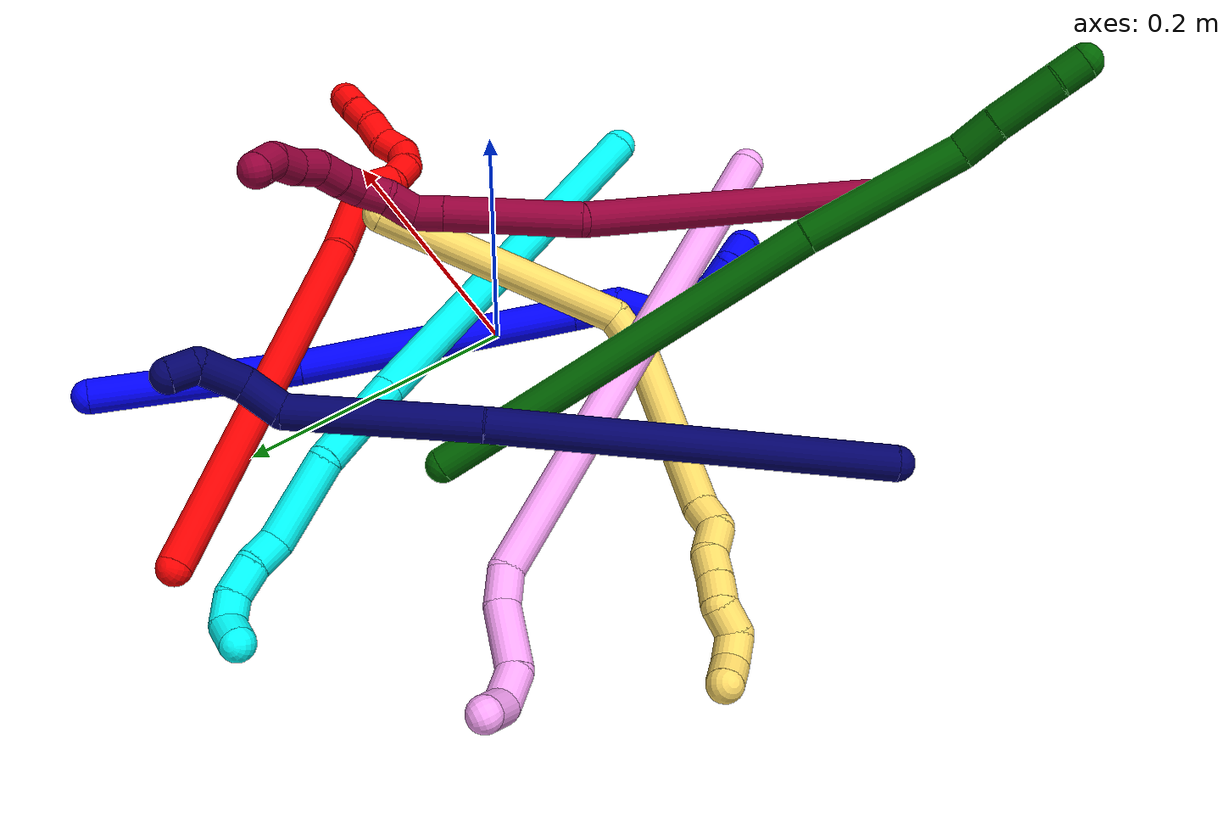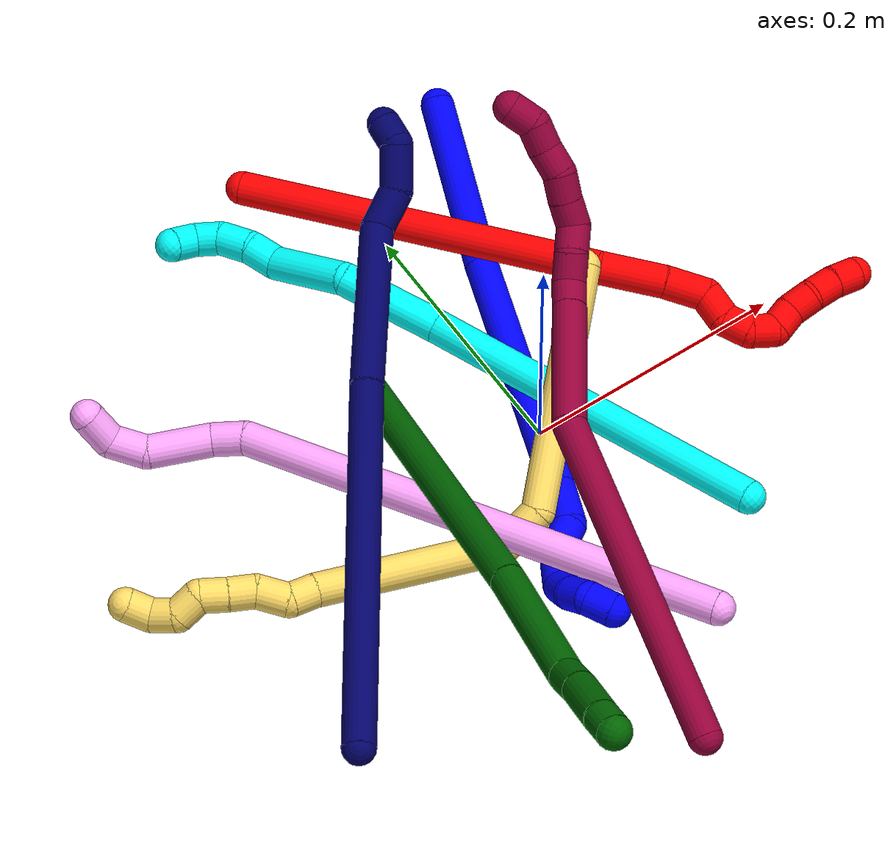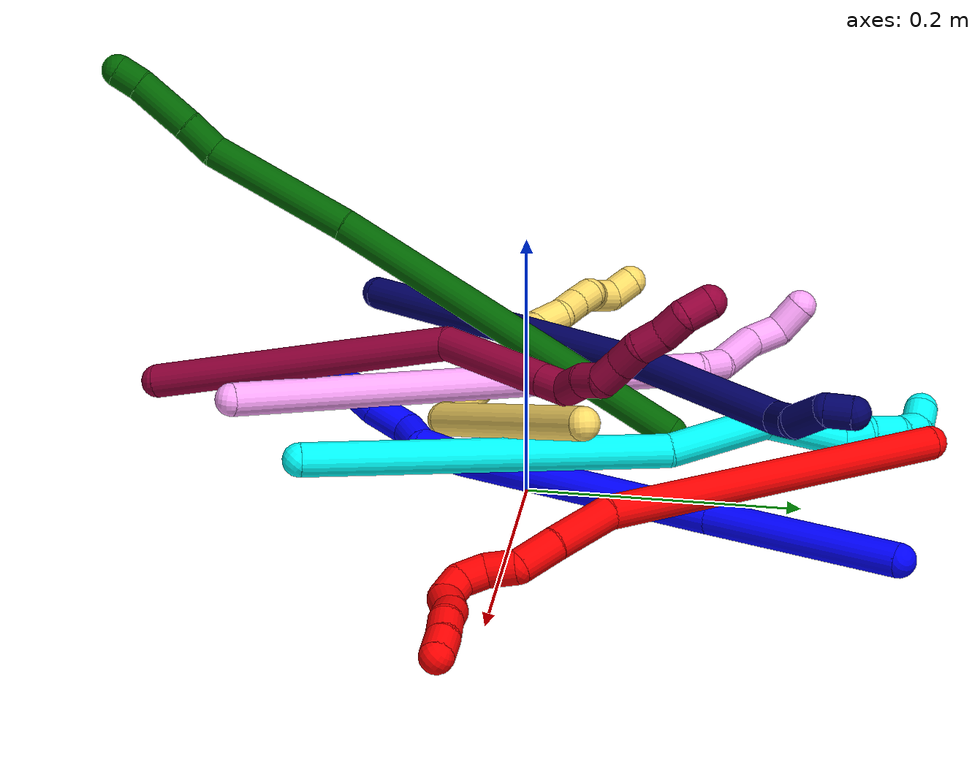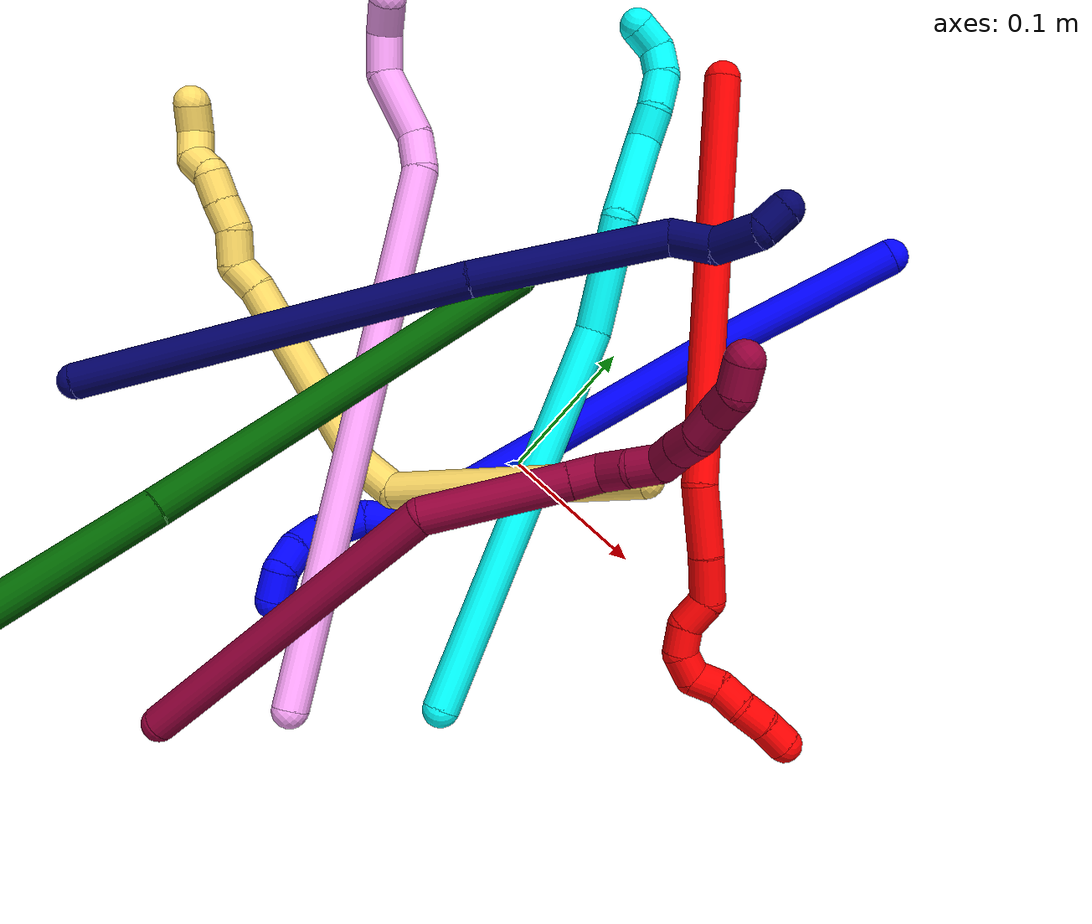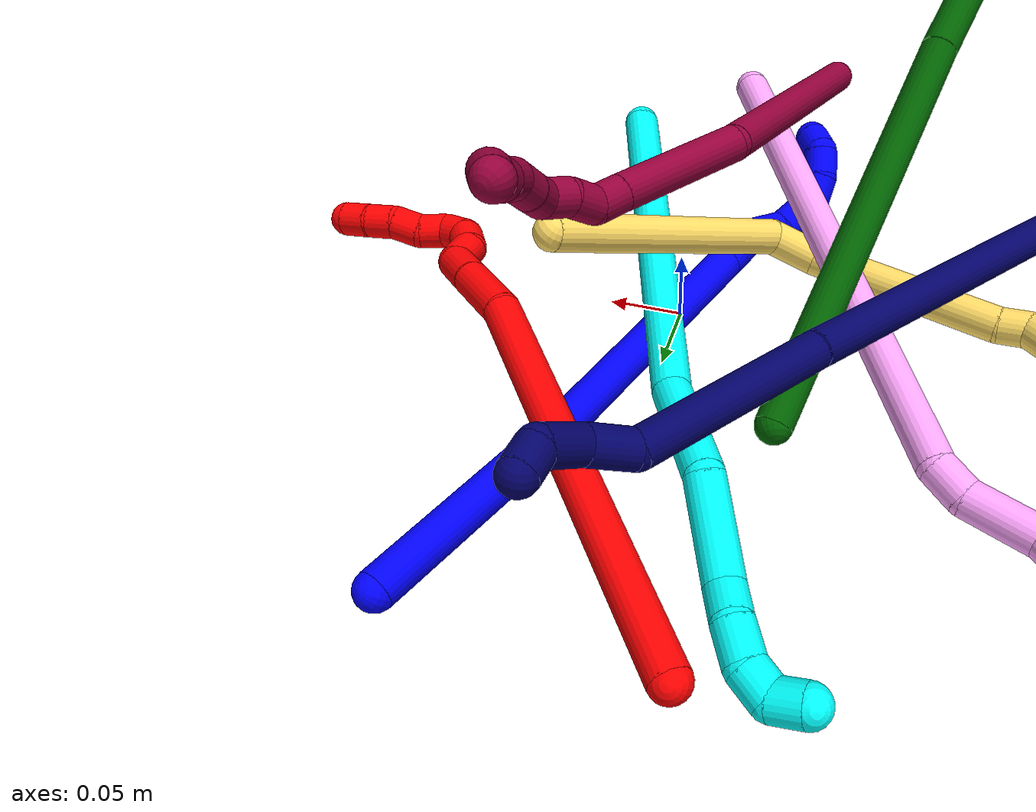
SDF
<sdf version="1.7">
 <world name="default">
  <plugin name="TubeGeneratorPlugin" filename="libtube_generator_plugin.so"/>
  <model name="photoneo_s_sensor">
   <static>1</static>
   <pose>0 0 2 1.57079 1.57079 3.14159</pose>
   <link name="link">
    <inertial><mass>0.1</mass></inertial>
    <sensor name="sensor" type="depth">
     <update_rate>30</update_rate>
     <camera>
      <horizontal_fov>1.22</horizontal_fov>
      <image><width>1920</width><height>1200</height><format>B8G8R8</format></image>
      <clip><near>0.1</near><far>4</far></clip>
      <depth_camera><output>points</output></depth_camera>
     </camera>
     <plugin name="camera_plugin" filename="libgazebo_ros_depth_camera.so">
      <baseline>0.2</baseline>
      <alwaysOn>1</alwaysOn>
      <updateRate>0.0</updateRate>
      <cameraName>camera_ir</cameraName>
      <imageTopicName>/camera/color/image_raw</imageTopicName>
      <cameraInfoTopicName>/camera/color/camera_info</cameraInfoTopicName>
      <depthImageTopicName>/camera/depth/image_raw</depthImageTopicName>
      <depthImageCameraInfoTopicName>/camera/depth/camera_info</depthImageCameraInfoTopicName>
      <pointCloudTopicName>/camera/depth/points</pointCloudTopicName>
      <frameName>fr_optical</frameName>
      <pointCloudCutoff>0.1</pointCloudCutoff>
      <pointCloudCutoffMax>2.0</pointCloudCutoffMax>
      <distortionK1>0</distortionK1>
      <distortionK2>0</distortionK2>
      <distortionK3>0</distortionK3>
      <distortionT1>0</distortionT1>
      <distortionT2>0</distortionT2>
      <CxPrime>0</CxPrime>
      <Cx>0</Cx>
      <Cy>0</Cy>
      <focalLength>0</focalLength>
      <hackBaseline>0</hackBaseline>
     </plugin>
    </sensor>
   </link>
  </model>
  <gravity>0 0 -9.8</gravity>
  <magnetic_field>6e-06 2.3e-05 -4.2e-05</magnetic_field>
  <atmosphere type="adiabatic"/>
  <physics name="default_physics" default="0" type="ode">
   <max_step_size>0.003</max_step_size>
   <real_time_factor>1</real_time_factor>
   <real_time_update_rate>1000</real_time_update_rate>
   <max_contacts>10000</max_contacts>
   <ode>
    <solver>
     <type>quick</type>
     <iters>100</iters>
     <sor>1.3</sor>
     <use_dynamic_moi_rescaling>0</use_dynamic_moi_rescaling>
    </solver>
    <constraints>
     <contact_max_correcting_vel>0</contact_max_correcting_vel>
     <contact_surface_layer>0.001</contact_surface_layer>
     <cfm>0</cfm>
     <erp>0.2</erp>
    </constraints>
   </ode>
  </physics>
  <scene><ambient>0.4 0.4 0.4 1</ambient><background>0.7 0.7 0.7 1</background><shadows>0</shadows></scene>
  <audio><device>default</device></audio>
  <spherical_coordinates>
   <surface_model>EARTH_WGS84</surface_model>
   <latitude_deg>0</latitude_deg>
   <longitude_deg>0</longitude_deg>
   <elevation>0</elevation>
   <heading_deg>0</heading_deg>
  </spherical_coordinates>
  <model name="bin">
   <static>1</static>
   <link name="bottom">
    <collision name="collision-bottom">
     <pose>0 0 -0.01 0 -0 0</pose>
     <geometry><box><size>0.8 0.6 0.02</size></box></geometry>
     <surface>
      <friction><ode><mu>100</mu><mu2>100</mu2></ode></friction>
      <contact><collide_bitmask>65535</collide_bitmask></contact>
     </surface>
    </collision>
   </link>
   <link name="west_wall">
    <collision name="collision-west_wall">
     <pose>-0.41 0 0.1 0 -0 0</pose>
     <geometry><box><size>0.02 0.6 0.2</size></box></geometry>
     <surface>
      <friction><ode><mu>100</mu><mu2>100</mu2></ode></friction>
      <contact><collide_bitmask>65535</collide_bitmask></contact>
     </surface>
    </collision>
   </link>
   <link name="east_wall">
    <collision name="collision-east_wall">
     <pose>0.41 0 0.1 0 -0 0</pose>
     <geometry><box><size>0.02 0.6 0.2</size></box></geometry>
     <surface>
      <friction><ode><mu>100</mu><mu2>100</mu2></ode></friction>
      <contact><collide_bitmask>65535</collide_bitmask></contact>
     </surface>
    </collision>
   </link>
   <link name="south_wall">
    <collision name="collision-south_wall">
     <pose>0 -0.31 0.1 0 -0 0</pose>
     <geometry><box><size>0.8 0.02 0.2</size></box></geometry>
     <surface>
      <friction><ode><mu>100</mu><mu2>100</mu2></ode></friction>
      <contact><collide_bitmask>65535</collide_bitmask></contact>
     </surface>
    </collision>
   </link>
   <link name="north_wall">
    <collision name="collision-north_wall">
     <pose>0 0.31 0.1 0 -0 0</pose>
     <geometry><box><size>0.8 0.02 0.2</size></box></geometry>
     <surface>
      <friction><ode><mu>100</mu><mu2>100</mu2></ode></friction>
      <contact><collide_bitmask>65535</collide_bitmask></contact>
     </surface>
    </collision>
   </link>
  </model>
  <model name="1">
   <static>0</static>
   <link name="1">
    <collision name="collision-cylinder-e_1_1_4">
     <pose>-0.018529 -0.052572 -0.048535 2.31629 -0.253398 -0.5663</pose>
     <geometry><cylinder><radius>0.0125</radius><length>0.147822</length></cylinder></geometry>
     <surface>
      <friction><ode><mu>1.16</mu><mu2>1.16</mu2><slip1>0</slip1><slip2>0</slip2></ode></friction>
      <contact><ode><kp>1e+06</kp><kd>1</kd><max_vel>0</max_vel><min_depth>0.001</min_depth></ode></contact>
     </surface>
    </collision>
    <visual name="visual-cylinder-e_1_1_4">
     <pose>-0.018529 -0.052572 -0.048535 2.31629 -0.253398 -0.5663</pose>
     <geometry><cylinder><radius>0.0125</radius><length>0.147822</length></cylinder></geometry>
     <material><ambient>0 0 1 1</ambient></material>
    </visual>
    <collision name="collision-cylinder-e_2_4_5">
     <pose>-0.060913 -0.180215 -0.158418 2.25592 -0.241266 -0.5005</pose>
     <geometry><cylinder><radius>0.0125</radius><length>0.199682</length></cylinder></geometry>
     <surface>
      <friction><ode><mu>1.16</mu><mu2>1.16</mu2><slip1>0</slip1><slip2>0</slip2></ode></friction>
      <contact><ode><kp>1e+06</kp><kd>1</kd><max_vel>0</max_vel><min_depth>0.001</min_depth></ode></contact>
     </surface>
    </collision>
    <visual name="visual-cylinder-e_2_4_5">
     <pose>-0.060913 -0.180215 -0.158418 2.25592 -0.241266 -0.5005</pose>
     <geometry><cylinder><radius>0.0125</radius><length>0.199682</length></cylinder></geometry>
     <material><ambient>0 0 1 1</ambient></material>
    </visual>
    <collision name="collision-cylinder-e_3_5_6">
     <pose>-0.09048 -0.268298 -0.229603 2.2182 -0.336804 -0.658503</pose>
     <geometry><cylinder><radius>0.0125</radius><length>0.034566</length></cylinder></geometry>
     <surface>
      <friction><ode><mu>1.16</mu><mu2>1.16</mu2><slip1>0</slip1><slip2>0</slip2></ode></friction>
      <contact><ode><kp>1e+06</kp><kd>1</kd><max_vel>0</max_vel><min_depth>0.001</min_depth></ode></contact>
     </surface>
    </collision>
    <visual name="visual-cylinder-e_3_5_6">
     <pose>-0.09048 -0.268298 -0.229603 2.2182 -0.336804 -0.658503</pose>
     <geometry><cylinder><radius>0.0125</radius><length>0.034566</length></cylinder></geometry>
     <material><ambient>0 0 1 1</ambient></material>
    </visual>
    <collision name="collision-cylinder-e_4_6_7">
     <pose>-0.104538 -0.284527 -0.247746 2.77196 -0.75288 -2.25806</pose>
     <geometry><cylinder><radius>0.0125</radius><length>0.024413</length></cylinder></geometry>
     <surface>
      <friction><ode><mu>1.16</mu><mu2>1.16</mu2><slip1>0</slip1><slip2>0</slip2></ode></friction>
      <contact><ode><kp>1e+06</kp><kd>1</kd><max_vel>0</max_vel><min_depth>0.001</min_depth></ode></contact>
     </surface>
    </collision>
    <visual name="visual-cylinder-e_4_6_7">
     <pose>-0.104538 -0.284527 -0.247746 2.77196 -0.75288 -2.25806</pose>
     <geometry><cylinder><radius>0.0125</radius><length>0.024413</length></cylinder></geometry>
     <material><ambient>0 0 1 1</ambient></material>
    </visual>
    <collision name="collision-cylinder-e_5_7_8">
     <pose>-0.121306 -0.29919 -0.264925 2.23027 -0.52679 -1.00608</pose>
     <geometry><cylinder><radius>0.0125</radius><length>0.033505</length></cylinder></geometry>
     <surface>
      <friction><ode><mu>1.16</mu><mu2>1.16</mu2><slip1>0</slip1><slip2>0</slip2></ode></friction>
      <contact><ode><kp>1e+06</kp><kd>1</kd><max_vel>0</max_vel><min_depth>0.001</min_depth></ode></contact>
     </surface>
    </collision>
    <visual name="visual-cylinder-e_5_7_8">
     <pose>-0.121306 -0.29919 -0.264925 2.23027 -0.52679 -1.00608</pose>
     <geometry><cylinder><radius>0.0125</radius><length>0.033505</length></cylinder></geometry>
     <material><ambient>0 0 1 1</ambient></material>
    </visual>
    <collision name="collision-cylinder-e_6_8_9">
     <pose>-0.134752 -0.319279 -0.273424 1.52764 -0.526018 -0.504743</pose>
     <geometry><cylinder><radius>0.0125</radius><length>0.02001</length></cylinder></geometry>
     <surface>
      <friction><ode><mu>1.16</mu><mu2>1.16</mu2><slip1>0</slip1><slip2>0</slip2></ode></friction>
      <contact><ode><kp>1e+06</kp><kd>1</kd><max_vel>0</max_vel><min_depth>0.001</min_depth></ode></contact>
     </surface>
    </collision>
    <visual name="visual-cylinder-e_6_8_9">
     <pose>-0.134752 -0.319279 -0.273424 1.52764 -0.526018 -0.504743</pose>
     <geometry><cylinder><radius>0.0125</radius><length>0.02001</length></cylinder></geometry>
     <material><ambient>0 0 1 1</ambient></material>
    </visual>
    <collision name="collision-cylinder-e_7_9_10">
     <pose>-0.141844 -0.337614 -0.271698 1.43206 -0.208351 -0.181439</pose>
     <geometry><cylinder><radius>0.0125</radius><length>0.020001</length></cylinder></geometry>
     <surface>
      <friction><ode><mu>1.16</mu><mu2>1.16</mu2><slip1>0</slip1><slip2>0</slip2></ode></friction>
      <contact><ode><kp>1e+06</kp><kd>1</kd><max_vel>0</max_vel><min_depth>0.001</min_depth></ode></contact>
     </surface>
    </collision>
    <visual name="visual-cylinder-e_7_9_10">
     <pose>-0.141844 -0.337614 -0.271698 1.43206 -0.208351 -0.181439</pose>
     <geometry><cylinder><radius>0.0125</radius><length>0.020001</length></cylinder></geometry>
     <material><ambient>0 0 1 1</ambient></material>
    </visual>
    <collision name="collision-cylinder-e_8_10_2">
     <pose>-0.140117 -0.356422 -0.271916 1.74142 0.38936 0.459834</pose>
     <geometry><cylinder><radius>0.0125</radius><length>0.020001</length></cylinder></geometry>
     <surface>
      <friction><ode><mu>1.16</mu><mu2>1.16</mu2><slip1>0</slip1><slip2>0</slip2></ode></friction>
      <contact><ode><kp>1e+06</kp><kd>1</kd><max_vel>0</max_vel><min_depth>0.001</min_depth></ode></contact>
     </surface>
    </collision>
    <visual name="visual-cylinder-e_8_10_2">
     <pose>-0.140117 -0.356422 -0.271916 1.74142 0.38936 0.459834</pose>
     <geometry><cylinder><radius>0.0125</radius><length>0.020001</length></cylinder></geometry>
     <material><ambient>0 0 1 1</ambient></material>
    </visual>
    <collision name="collision-sphere-2">
     <pose>-0.136321 -0.36554 -0.273487 0 -0 0</pose>
     <geometry><sphere><radius>0.0125</radius></sphere></geometry>
     <surface>
      <friction><ode><mu>1.16</mu><mu2>1.16</mu2><slip1>0</slip1><slip2>0</slip2></ode></friction>
      <contact><ode><kp>1e+06</kp><kd>1</kd><max_vel>0</max_vel><min_depth>0.001</min_depth></ode></contact>
     </surface>
    </collision>
    <visual name="visual-sphere-2">
     <pose>-0.136321 -0.36554 -0.273487 0 -0 0</pose>
     <geometry><sphere><radius>0.0125</radius></sphere></geometry>
     <material><ambient>0 0 1 1</ambient></material>
    </visual>
    <collision name="collision-sphere-10">
     <pose>-0.143913 -0.347304 -0.270345 0 -0 0</pose>
     <geometry><sphere><radius>0.0125</radius></sphere></geometry>
     <surface>
      <friction><ode><mu>1.16</mu><mu2>1.16</mu2><slip1>0</slip1><slip2>0</slip2></ode></friction>
      <contact><ode><kp>1e+06</kp><kd>1</kd><max_vel>0</max_vel><min_depth>0.001</min_depth></ode></contact>
     </surface>
    </collision>
    <visual name="visual-sphere-10">
     <pose>-0.143913 -0.347304 -0.270345 0 -0 0</pose>
     <geometry><sphere><radius>0.0125</radius></sphere></geometry>
     <material><ambient>0 0 1 1</ambient></material>
    </visual>
    <collision name="collision-sphere-9">
     <pose>-0.139776 -0.327924 -0.273051 0 -0 0</pose>
     <geometry><sphere><radius>0.0125</radius></sphere></geometry>
     <surface>
      <friction><ode><mu>1.16</mu><mu2>1.16</mu2><slip1>0</slip1><slip2>0</slip2></ode></friction>
      <contact><ode><kp>1e+06</kp><kd>1</kd><max_vel>0</max_vel><min_depth>0.001</min_depth></ode></contact>
     </surface>
    </collision>
    <visual name="visual-sphere-9">
     <pose>-0.139776 -0.327924 -0.273051 0 -0 0</pose>
     <geometry><sphere><radius>0.0125</radius></sphere></geometry>
     <material><ambient>0 0 1 1</ambient></material>
    </visual>
    <collision name="collision-sphere-4">
     <pose>-0.037058 -0.105144 -0.097071 0 -0 0</pose>
     <geometry><sphere><radius>0.0125</radius></sphere></geometry>
     <surface>
      <friction><ode><mu>1.16</mu><mu2>1.16</mu2><slip1>0</slip1><slip2>0</slip2></ode></friction>
      <contact><ode><kp>1e+06</kp><kd>1</kd><max_vel>0</max_vel><min_depth>0.001</min_depth></ode></contact>
     </surface>
    </collision>
    <visual name="visual-sphere-4">
     <pose>-0.037058 -0.105144 -0.097071 0 -0 0</pose>
     <geometry><sphere><radius>0.0125</radius></sphere></geometry>
     <material><ambient>0 0 1 1</ambient></material>
    </visual>
    <collision name="collision-sphere-1">
     <geometry><sphere><radius>0.0125</radius></sphere></geometry>
     <surface>
      <friction><ode><mu>1.16</mu><mu2>1.16</mu2><slip1>0</slip1><slip2>0</slip2></ode></friction>
      <contact><ode><kp>1e+06</kp><kd>1</kd><max_vel>0</max_vel><min_depth>0.001</min_depth></ode></contact>
     </surface>
    </collision>
    <visual name="visual-sphere-1">
     <geometry><sphere><radius>0.0125</radius></sphere></geometry>
     <material><ambient>0 0 1 1</ambient></material>
    </visual>
    <collision name="collision-sphere-8">
     <pose>-0.129729 -0.310635 -0.273797 0 -0 0</pose>
     <geometry><sphere><radius>0.0125</radius></sphere></geometry>
     <surface>
      <friction><ode><mu>1.16</mu><mu2>1.16</mu2><slip1>0</slip1><slip2>0</slip2></ode></friction>
      <contact><ode><kp>1e+06</kp><kd>1</kd><max_vel>0</max_vel><min_depth>0.001</min_depth></ode></contact>
     </surface>
    </collision>
    <visual name="visual-sphere-8">
     <pose>-0.129729 -0.310635 -0.273797 0 -0 0</pose>
     <geometry><sphere><radius>0.0125</radius></sphere></geometry>
     <material><ambient>0 0 1 1</ambient></material>
    </visual>
    <collision name="collision-sphere-5">
     <pose>-0.084769 -0.255287 -0.219765 0 -0 0</pose>
     <geometry><sphere><radius>0.0125</radius></sphere></geometry>
     <surface>
      <friction><ode><mu>1.16</mu><mu2>1.16</mu2><slip1>0</slip1><slip2>0</slip2></ode></friction>
      <contact><ode><kp>1e+06</kp><kd>1</kd><max_vel>0</max_vel><min_depth>0.001</min_depth></ode></contact>
     </surface>
    </collision>
    <visual name="visual-sphere-5">
     <pose>-0.084769 -0.255287 -0.219765 0 -0 0</pose>
     <geometry><sphere><radius>0.0125</radius></sphere></geometry>
     <material><ambient>0 0 1 1</ambient></material>
    </visual>
    <collision name="collision-sphere-6">
     <pose>-0.096192 -0.28131 -0.239441 0 -0 0</pose>
     <geometry><sphere><radius>0.0125</radius></sphere></geometry>
     <surface>
      <friction><ode><mu>1.16</mu><mu2>1.16</mu2><slip1>0</slip1><slip2>0</slip2></ode></friction>
      <contact><ode><kp>1e+06</kp><kd>1</kd><max_vel>0</max_vel><min_depth>0.001</min_depth></ode></contact>
     </surface>
    </collision>
    <visual name="visual-sphere-6">
     <pose>-0.096192 -0.28131 -0.239441 0 -0 0</pose>
     <geometry><sphere><radius>0.0125</radius></sphere></geometry>
     <material><ambient>0 0 1 1</ambient></material>
    </visual>
    <collision name="collision-sphere-7">
     <pose>-0.112884 -0.287745 -0.256052 0 -0 0</pose>
     <geometry><sphere><radius>0.0125</radius></sphere></geometry>
     <surface>
      <friction><ode><mu>1.16</mu><mu2>1.16</mu2><slip1>0</slip1><slip2>0</slip2></ode></friction>
      <contact><ode><kp>1e+06</kp><kd>1</kd><max_vel>0</max_vel><min_depth>0.001</min_depth></ode></contact>
     </surface>
    </collision>
    <visual name="visual-sphere-7">
     <pose>-0.112884 -0.287745 -0.256052 0 -0 0</pose>
     <geometry><sphere><radius>0.0125</radius></sphere></geometry>
     <material><ambient>0 0 1 1</ambient></material>
    </visual>
    <inertial>
     <pose>-0.065964 -0.180544 -0.156026 0 -0 0</pose>
     <mass>0.5</mass>
     <inertia>
      <ixx>0.000331</ixx>
      <ixy>0</ixy>
      <ixz>0</ixz>
      <iyy>-0.000934</iyy>
      <iyz>0</iyz>
      <izz>0.000925</izz>
     </inertia>
    </inertial>
   </link>
   <pose>0.097172 0.275657 0.016848 -0.483097 0.684025 -0.010634</pose>
  </model>
  <model name="2">
   <static>0</static>
   <link name="2">
    <collision name="collision-cylinder-e_1_1_4">
     <pose>0.083787 -0.086686 -0.066794 2.22731 0.653432 1.20645</pose>
     <geometry><cylinder><radius>0.0125</radius><length>0.275653</length></cylinder></geometry>
     <surface>
      <friction><ode><mu>1.16</mu><mu2>1.16</mu2><slip1>0</slip1><slip2>0</slip2></ode></friction>
      <contact><ode><kp>1e+06</kp><kd>1</kd><max_vel>0</max_vel><min_depth>0.001</min_depth></ode></contact>
     </surface>
    </collision>
    <visual name="visual-cylinder-e_1_1_4">
     <pose>0.083787 -0.086686 -0.066794 2.22731 0.653432 1.20645</pose>
     <geometry><cylinder><radius>0.0125</radius><length>0.275653</length></cylinder></geometry>
     <material><ambient>1 0 0 1</ambient></material>
    </visual>
    <collision name="collision-cylinder-e_2_4_5">
     <pose>0.184751 -0.182997 -0.148008 2.55304 0.780758 1.87197</pose>
     <geometry><cylinder><radius>0.0125</radius><length>0.048812</length></cylinder></geometry>
     <surface>
      <friction><ode><mu>1.16</mu><mu2>1.16</mu2><slip1>0</slip1><slip2>0</slip2></ode></friction>
      <contact><ode><kp>1e+06</kp><kd>1</kd><max_vel>0</max_vel><min_depth>0.001</min_depth></ode></contact>
     </surface>
    </collision>
    <visual name="visual-cylinder-e_2_4_5">
     <pose>0.184751 -0.182997 -0.148008 2.55304 0.780758 1.87197</pose>
     <geometry><cylinder><radius>0.0125</radius><length>0.048812</length></cylinder></geometry>
     <material><ambient>1 0 0 1</ambient></material>
    </visual>
    <collision name="collision-cylinder-e_3_5_6">
     <pose>0.212409 -0.198506 -0.173131 2.6389 0.709194 1.92886</pose>
     <geometry><cylinder><radius>0.0125</radius><length>0.032186</length></cylinder></geometry>
     <surface>
      <friction><ode><mu>1.16</mu><mu2>1.16</mu2><slip1>0</slip1><slip2>0</slip2></ode></friction>
      <contact><ode><kp>1e+06</kp><kd>1</kd><max_vel>0</max_vel><min_depth>0.001</min_depth></ode></contact>
     </surface>
    </collision>
    <visual name="visual-cylinder-e_3_5_6">
     <pose>0.212409 -0.198506 -0.173131 2.6389 0.709194 1.92886</pose>
     <geometry><cylinder><radius>0.0125</radius><length>0.032186</length></cylinder></geometry>
     <material><ambient>1 0 0 1</ambient></material>
    </visual>
    <collision name="collision-cylinder-e_4_6_7">
     <pose>0.222633 -0.211726 -0.192777 2.45462 -0.022142 -0.06189</pose>
     <geometry><cylinder><radius>0.0125</radius><length>0.023141</length></cylinder></geometry>
     <surface>
      <friction><ode><mu>1.16</mu><mu2>1.16</mu2><slip1>0</slip1><slip2>0</slip2></ode></friction>
      <contact><ode><kp>1e+06</kp><kd>1</kd><max_vel>0</max_vel><min_depth>0.001</min_depth></ode></contact>
     </surface>
    </collision>
    <visual name="visual-cylinder-e_4_6_7">
     <pose>0.222633 -0.211726 -0.192777 2.45462 -0.022142 -0.06189</pose>
     <geometry><cylinder><radius>0.0125</radius><length>0.023141</length></cylinder></geometry>
     <material><ambient>1 0 0 1</ambient></material>
    </visual>
    <collision name="collision-cylinder-e_5_7_8">
     <pose>0.227323 -0.224412 -0.208685 2.48659 0.51304 1.31495</pose>
     <geometry><cylinder><radius>0.0125</radius><length>0.020157</length></cylinder></geometry>
     <surface>
      <friction><ode><mu>1.16</mu><mu2>1.16</mu2><slip1>0</slip1><slip2>0</slip2></ode></friction>
      <contact><ode><kp>1e+06</kp><kd>1</kd><max_vel>0</max_vel><min_depth>0.001</min_depth></ode></contact>
     </surface>
    </collision>
    <visual name="visual-cylinder-e_5_7_8">
     <pose>0.227323 -0.224412 -0.208685 2.48659 0.51304 1.31495</pose>
     <geometry><cylinder><radius>0.0125</radius><length>0.020157</length></cylinder></geometry>
     <material><ambient>1 0 0 1</ambient></material>
    </visual>
    <collision name="collision-cylinder-e_6_8_9">
     <pose>0.241085 -0.230886 -0.220245 2.90148 1.07805 2.74354</pose>
     <geometry><cylinder><radius>0.0125</radius><length>0.020009</length></cylinder></geometry>
     <surface>
      <friction><ode><mu>1.16</mu><mu2>1.16</mu2><slip1>0</slip1><slip2>0</slip2></ode></friction>
      <contact><ode><kp>1e+06</kp><kd>1</kd><max_vel>0</max_vel><min_depth>0.001</min_depth></ode></contact>
     </surface>
    </collision>
    <visual name="visual-cylinder-e_6_8_9">
     <pose>0.241085 -0.230886 -0.220245 2.90148 1.07805 2.74354</pose>
     <geometry><cylinder><radius>0.0125</radius><length>0.020009</length></cylinder></geometry>
     <material><ambient>1 0 0 1</ambient></material>
    </visual>
    <collision name="collision-cylinder-e_7_9_10">
     <pose>0.259322 -0.229255 -0.222914 -0.960619 1.22789 -0.703845</pose>
     <geometry><cylinder><radius>0.0125</radius><length>0.020011</length></cylinder></geometry>
     <surface>
      <friction><ode><mu>1.16</mu><mu2>1.16</mu2><slip1>0</slip1><slip2>0</slip2></ode></friction>
      <contact><ode><kp>1e+06</kp><kd>1</kd><max_vel>0</max_vel><min_depth>0.001</min_depth></ode></contact>
     </surface>
    </collision>
    <visual name="visual-cylinder-e_7_9_10">
     <pose>0.259322 -0.229255 -0.222914 -0.960619 1.22789 -0.703845</pose>
     <geometry><cylinder><radius>0.0125</radius><length>0.020011</length></cylinder></geometry>
     <material><ambient>1 0 0 1</ambient></material>
    </visual>
    <collision name="collision-cylinder-e_8_10_11">
     <pose>0.278666 -0.227477 -0.220031 0.797457 1.43368 0.703748</pose>
     <geometry><cylinder><radius>0.0125</radius><length>0.020029</length></cylinder></geometry>
     <surface>
      <friction><ode><mu>1.16</mu><mu2>1.16</mu2><slip1>0</slip1><slip2>0</slip2></ode></friction>
      <contact><ode><kp>1e+06</kp><kd>1</kd><max_vel>0</max_vel><min_depth>0.001</min_depth></ode></contact>
     </surface>
    </collision>
    <visual name="visual-cylinder-e_8_10_11">
     <pose>0.278666 -0.227477 -0.220031 0.797457 1.43368 0.703748</pose>
     <geometry><cylinder><radius>0.0125</radius><length>0.020029</length></cylinder></geometry>
     <material><ambient>1 0 0 1</ambient></material>
    </visual>
    <collision name="collision-cylinder-e_9_11_12">
     <pose>0.298477 -0.227161 -0.219778 -2.06811 1.4228 -1.93324</pose>
     <geometry><cylinder><radius>0.0125</radius><length>0.02</length></cylinder></geometry>
     <surface>
      <friction><ode><mu>1.16</mu><mu2>1.16</mu2><slip1>0</slip1><slip2>0</slip2></ode></friction>
      <contact><ode><kp>1e+06</kp><kd>1</kd><max_vel>0</max_vel><min_depth>0.001</min_depth></ode></contact>
     </surface>
    </collision>
    <visual name="visual-cylinder-e_9_11_12">
     <pose>0.298477 -0.227161 -0.219778 -2.06811 1.4228 -1.93324</pose>
     <geometry><cylinder><radius>0.0125</radius><length>0.02</length></cylinder></geometry>
     <material><ambient>1 0 0 1</ambient></material>
    </visual>
    <collision name="collision-cylinder-e_10_12_2">
     <pose>0.318089 -0.22498 -0.222654 -2.75467 1.33399 -2.65387</pose>
     <geometry><cylinder><radius>0.0125</radius><length>0.02</length></cylinder></geometry>
     <surface>
      <friction><ode><mu>1.16</mu><mu2>1.16</mu2><slip1>0</slip1><slip2>0</slip2></ode></friction>
      <contact><ode><kp>1e+06</kp><kd>1</kd><max_vel>0</max_vel><min_depth>0.001</min_depth></ode></contact>
     </surface>
    </collision>
    <visual name="visual-cylinder-e_10_12_2">
     <pose>0.318089 -0.22498 -0.222654 -2.75467 1.33399 -2.65387</pose>
     <geometry><cylinder><radius>0.0125</radius><length>0.02</length></cylinder></geometry>
     <material><ambient>1 0 0 1</ambient></material>
    </visual>
    <collision name="collision-sphere-2">
     <pose>0.32781 -0.224094 -0.224826 0 -0 0</pose>
     <geometry><sphere><radius>0.0125</radius></sphere></geometry>
     <surface>
      <friction><ode><mu>1.16</mu><mu2>1.16</mu2><slip1>0</slip1><slip2>0</slip2></ode></friction>
      <contact><ode><kp>1e+06</kp><kd>1</kd><max_vel>0</max_vel><min_depth>0.001</min_depth></ode></contact>
     </surface>
    </collision>
    <visual name="visual-sphere-2">
     <pose>0.32781 -0.224094 -0.224826 0 -0 0</pose>
     <geometry><sphere><radius>0.0125</radius></sphere></geometry>
     <material><ambient>1 0 0 1</ambient></material>
    </visual>
    <collision name="collision-sphere-12">
     <pose>0.308368 -0.225865 -0.220481 0 -0 0</pose>
     <geometry><sphere><radius>0.0125</radius></sphere></geometry>
     <surface>
      <friction><ode><mu>1.16</mu><mu2>1.16</mu2><slip1>0</slip1><slip2>0</slip2></ode></friction>
      <contact><ode><kp>1e+06</kp><kd>1</kd><max_vel>0</max_vel><min_depth>0.001</min_depth></ode></contact>
     </surface>
    </collision>
    <visual name="visual-sphere-12">
     <pose>0.308368 -0.225865 -0.220481 0 -0 0</pose>
     <geometry><sphere><radius>0.0125</radius></sphere></geometry>
     <material><ambient>1 0 0 1</ambient></material>
    </visual>
    <collision name="collision-sphere-11">
     <pose>0.288586 -0.228457 -0.219074 0 -0 0</pose>
     <geometry><sphere><radius>0.0125</radius></sphere></geometry>
     <surface>
      <friction><ode><mu>1.16</mu><mu2>1.16</mu2><slip1>0</slip1><slip2>0</slip2></ode></friction>
      <contact><ode><kp>1e+06</kp><kd>1</kd><max_vel>0</max_vel><min_depth>0.001</min_depth></ode></contact>
     </surface>
    </collision>
    <visual name="visual-sphere-11">
     <pose>0.288586 -0.228457 -0.219074 0 -0 0</pose>
     <geometry><sphere><radius>0.0125</radius></sphere></geometry>
     <material><ambient>1 0 0 1</ambient></material>
    </visual>
    <collision name="collision-sphere-10">
     <pose>0.268746 -0.226498 -0.220987 0 -0 0</pose>
     <geometry><sphere><radius>0.0125</radius></sphere></geometry>
     <surface>
      <friction><ode><mu>1.16</mu><mu2>1.16</mu2><slip1>0</slip1><slip2>0</slip2></ode></friction>
      <contact><ode><kp>1e+06</kp><kd>1</kd><max_vel>0</max_vel><min_depth>0.001</min_depth></ode></contact>
     </surface>
    </collision>
    <visual name="visual-sphere-10">
     <pose>0.268746 -0.226498 -0.220987 0 -0 0</pose>
     <geometry><sphere><radius>0.0125</radius></sphere></geometry>
     <material><ambient>1 0 0 1</ambient></material>
    </visual>
    <collision name="collision-sphere-9">
     <pose>0.249899 -0.232012 -0.224842 0 -0 0</pose>
     <geometry><sphere><radius>0.0125</radius></sphere></geometry>
     <surface>
      <friction><ode><mu>1.16</mu><mu2>1.16</mu2><slip1>0</slip1><slip2>0</slip2></ode></friction>
      <contact><ode><kp>1e+06</kp><kd>1</kd><max_vel>0</max_vel><min_depth>0.001</min_depth></ode></contact>
     </surface>
    </collision>
    <visual name="visual-sphere-9">
     <pose>0.249899 -0.232012 -0.224842 0 -0 0</pose>
     <geometry><sphere><radius>0.0125</radius></sphere></geometry>
     <material><ambient>1 0 0 1</ambient></material>
    </visual>
    <collision name="collision-sphere-4">
     <pose>0.167573 -0.173372 -0.133588 0 -0 0</pose>
     <geometry><sphere><radius>0.0125</radius></sphere></geometry>
     <surface>
      <friction><ode><mu>1.16</mu><mu2>1.16</mu2><slip1>0</slip1><slip2>0</slip2></ode></friction>
      <contact><ode><kp>1e+06</kp><kd>1</kd><max_vel>0</max_vel><min_depth>0.001</min_depth></ode></contact>
     </surface>
    </collision>
    <visual name="visual-sphere-4">
     <pose>0.167573 -0.173372 -0.133588 0 -0 0</pose>
     <geometry><sphere><radius>0.0125</radius></sphere></geometry>
     <material><ambient>1 0 0 1</ambient></material>
    </visual>
    <collision name="collision-sphere-1">
     <geometry><sphere><radius>0.0125</radius></sphere></geometry>
     <surface>
      <friction><ode><mu>1.16</mu><mu2>1.16</mu2><slip1>0</slip1><slip2>0</slip2></ode></friction>
      <contact><ode><kp>1e+06</kp><kd>1</kd><max_vel>0</max_vel><min_depth>0.001</min_depth></ode></contact>
     </surface>
    </collision>
    <visual name="visual-sphere-1">
     <geometry><sphere><radius>0.0125</radius></sphere></geometry>
     <material><ambient>1 0 0 1</ambient></material>
    </visual>
    <collision name="collision-sphere-8">
     <pose>0.23227 -0.229761 -0.215648 0 -0 0</pose>
     <geometry><sphere><radius>0.0125</radius></sphere></geometry>
     <surface>
      <friction><ode><mu>1.16</mu><mu2>1.16</mu2><slip1>0</slip1><slip2>0</slip2></ode></friction>
      <contact><ode><kp>1e+06</kp><kd>1</kd><max_vel>0</max_vel><min_depth>0.001</min_depth></ode></contact>
     </surface>
    </collision>
    <visual name="visual-sphere-8">
     <pose>0.23227 -0.229761 -0.215648 0 -0 0</pose>
     <geometry><sphere><radius>0.0125</radius></sphere></geometry>
     <material><ambient>1 0 0 1</ambient></material>
    </visual>
    <collision name="collision-sphere-5">
     <pose>0.201928 -0.192622 -0.162429 0 -0 0</pose>
     <geometry><sphere><radius>0.0125</radius></sphere></geometry>
     <surface>
      <friction><ode><mu>1.16</mu><mu2>1.16</mu2><slip1>0</slip1><slip2>0</slip2></ode></friction>
      <contact><ode><kp>1e+06</kp><kd>1</kd><max_vel>0</max_vel><min_depth>0.001</min_depth></ode></contact>
     </surface>
    </collision>
    <visual name="visual-sphere-5">
     <pose>0.201928 -0.192622 -0.162429 0 -0 0</pose>
     <geometry><sphere><radius>0.0125</radius></sphere></geometry>
     <material><ambient>1 0 0 1</ambient></material>
    </visual>
    <collision name="collision-sphere-6">
     <pose>0.222889 -0.20439 -0.183833 0 -0 0</pose>
     <geometry><sphere><radius>0.0125</radius></sphere></geometry>
     <surface>
      <friction><ode><mu>1.16</mu><mu2>1.16</mu2><slip1>0</slip1><slip2>0</slip2></ode></friction>
      <contact><ode><kp>1e+06</kp><kd>1</kd><max_vel>0</max_vel><min_depth>0.001</min_depth></ode></contact>
     </surface>
    </collision>
    <visual name="visual-sphere-6">
     <pose>0.222889 -0.20439 -0.183833 0 -0 0</pose>
     <geometry><sphere><radius>0.0125</radius></sphere></geometry>
     <material><ambient>1 0 0 1</ambient></material>
    </visual>
    <collision name="collision-sphere-7">
     <pose>0.222376 -0.219063 -0.201721 0 -0 0</pose>
     <geometry><sphere><radius>0.0125</radius></sphere></geometry>
     <surface>
      <friction><ode><mu>1.16</mu><mu2>1.16</mu2><slip1>0</slip1><slip2>0</slip2></ode></friction>
      <contact><ode><kp>1e+06</kp><kd>1</kd><max_vel>0</max_vel><min_depth>0.001</min_depth></ode></contact>
     </surface>
    </collision>
    <visual name="visual-sphere-7">
     <pose>0.222376 -0.219063 -0.201721 0 -0 0</pose>
     <geometry><sphere><radius>0.0125</radius></sphere></geometry>
     <material><ambient>1 0 0 1</ambient></material>
    </visual>
    <inertial>
     <pose>0.153222 -0.142893 -0.124 0 -0 0</pose>
     <mass>0.5</mass>
     <inertia><ixx>0.001835</ixx><ixy>0</ixy><ixz>0</ixz><iyy>0.001721</iyy><iyz>0</iyz><izz>9e-06</izz></inertia>
    </inertial>
   </link>
   <pose>-0.068388 0.288503 0.025147 -0.680235 -0.063992 0.014559</pose>
  </model>
  <model name="3">
   <static>0</static>
   <link name="3">
    <collision name="collision-cylinder-e_1_1_4">
     <pose>-0.031854 0.103169 0.082612 -0.895601 -0.236498 0.11401</pose>
     <geometry><cylinder><radius>0.0125</radius><length>0.271907</length></cylinder></geometry>
     <surface>
      <friction><ode><mu>1.16</mu><mu2>1.16</mu2><slip1>0</slip1><slip2>0</slip2></ode></friction>
      <contact><ode><kp>1e+06</kp><kd>1</kd><max_vel>0</max_vel><min_depth>0.001</min_depth></ode></contact>
     </surface>
    </collision>
    <visual name="visual-cylinder-e_1_1_4">
     <pose>-0.031854 0.103169 0.082612 -0.895601 -0.236498 0.11401</pose>
     <geometry><cylinder><radius>0.0125</radius><length>0.271907</length></cylinder></geometry>
     <material><ambient>0.003922 1 0.996078 1</ambient></material>
    </visual>
    <collision name="collision-cylinder-e_2_4_5">
     <pose>-0.074943 0.22834 0.194847 -0.638824 -0.295579 0.098397</pose>
     <geometry><cylinder><radius>0.0125</radius><length>0.077142</length></cylinder></geometry>
     <surface>
      <friction><ode><mu>1.16</mu><mu2>1.16</mu2><slip1>0</slip1><slip2>0</slip2></ode></friction>
      <contact><ode><kp>1e+06</kp><kd>1</kd><max_vel>0</max_vel><min_depth>0.001</min_depth></ode></contact>
     </surface>
    </collision>
    <visual name="visual-cylinder-e_2_4_5">
     <pose>-0.074943 0.22834 0.194847 -0.638824 -0.295579 0.098397</pose>
     <geometry><cylinder><radius>0.0125</radius><length>0.077142</length></cylinder></geometry>
     <material><ambient>0.003922 1 0.996078 1</ambient></material>
    </visual>
    <collision name="collision-cylinder-e_3_5_6">
     <pose>-0.098805 0.27697 0.235922 -1.16461 -0.410788 0.272659</pose>
     <geometry><cylinder><radius>0.0125</radius><length>0.063237</length></cylinder></geometry>
     <surface>
      <friction><ode><mu>1.16</mu><mu2>1.16</mu2><slip1>0</slip1><slip2>0</slip2></ode></friction>
      <contact><ode><kp>1e+06</kp><kd>1</kd><max_vel>0</max_vel><min_depth>0.001</min_depth></ode></contact>
     </surface>
    </collision>
    <visual name="visual-cylinder-e_3_5_6">
     <pose>-0.098805 0.27697 0.235922 -1.16461 -0.410788 0.272659</pose>
     <geometry><cylinder><radius>0.0125</radius><length>0.063237</length></cylinder></geometry>
     <material><ambient>0.003922 1 0.996078 1</ambient></material>
    </visual>
    <collision name="collision-cylinder-e_4_6_7">
     <pose>-0.113862 0.310896 0.255877 -0.709266 -0.213648 0.079372</pose>
     <geometry><cylinder><radius>0.0125</radius><length>0.022929</length></cylinder></geometry>
     <surface>
      <friction><ode><mu>1.16</mu><mu2>1.16</mu2><slip1>0</slip1><slip2>0</slip2></ode></friction>
      <contact><ode><kp>1e+06</kp><kd>1</kd><max_vel>0</max_vel><min_depth>0.001</min_depth></ode></contact>
     </surface>
    </collision>
    <visual name="visual-cylinder-e_4_6_7">
     <pose>-0.113862 0.310896 0.255877 -0.709266 -0.213648 0.079372</pose>
     <geometry><cylinder><radius>0.0125</radius><length>0.022929</length></cylinder></geometry>
     <material><ambient>0.003922 1 0.996078 1</ambient></material>
    </visual>
    <collision name="collision-cylinder-e_5_7_8">
     <pose>-0.121259 0.327247 0.271154 -0.928438 -0.413825 0.209448</pose>
     <geometry><cylinder><radius>0.0125</radius><length>0.024702</length></cylinder></geometry>
     <surface>
      <friction><ode><mu>1.16</mu><mu2>1.16</mu2><slip1>0</slip1><slip2>0</slip2></ode></friction>
      <contact><ode><kp>1e+06</kp><kd>1</kd><max_vel>0</max_vel><min_depth>0.001</min_depth></ode></contact>
     </surface>
    </collision>
    <visual name="visual-cylinder-e_5_7_8">
     <pose>-0.121259 0.327247 0.271154 -0.928438 -0.413825 0.209448</pose>
     <geometry><cylinder><radius>0.0125</radius><length>0.024702</length></cylinder></geometry>
     <material><ambient>0.003922 1 0.996078 1</ambient></material>
    </visual>
    <collision name="collision-cylinder-e_6_8_9">
     <pose>-0.133441 0.341273 0.282828 -0.792646 -0.801926 0.351146</pose>
     <geometry><cylinder><radius>0.0125</radius><length>0.020077</length></cylinder></geometry>
     <surface>
      <friction><ode><mu>1.16</mu><mu2>1.16</mu2><slip1>0</slip1><slip2>0</slip2></ode></friction>
      <contact><ode><kp>1e+06</kp><kd>1</kd><max_vel>0</max_vel><min_depth>0.001</min_depth></ode></contact>
     </surface>
    </collision>
    <visual name="visual-cylinder-e_6_8_9">
     <pose>-0.133441 0.341273 0.282828 -0.792646 -0.801926 0.351146</pose>
     <geometry><cylinder><radius>0.0125</radius><length>0.020077</length></cylinder></geometry>
     <material><ambient>0.003922 1 0.996078 1</ambient></material>
    </visual>
    <collision name="collision-cylinder-e_7_9_2">
     <pose>-0.148254 0.343935 0.293809 0.362919 -0.862874 -0.168532</pose>
     <geometry><cylinder><radius>0.0125</radius><length>0.020006</length></cylinder></geometry>
     <surface>
      <friction><ode><mu>1.16</mu><mu2>1.16</mu2><slip1>0</slip1><slip2>0</slip2></ode></friction>
      <contact><ode><kp>1e+06</kp><kd>1</kd><max_vel>0</max_vel><min_depth>0.001</min_depth></ode></contact>
     </surface>
    </collision>
    <visual name="visual-cylinder-e_7_9_2">
     <pose>-0.148254 0.343935 0.293809 0.362919 -0.862874 -0.168532</pose>
     <geometry><cylinder><radius>0.0125</radius><length>0.020006</length></cylinder></geometry>
     <material><ambient>0.003922 1 0.996078 1</ambient></material>
    </visual>
    <collision name="collision-sphere-2">
     <pose>-0.155854 0.341626 0.299889 0 -0 0</pose>
     <geometry><sphere><radius>0.0125</radius></sphere></geometry>
     <surface>
      <friction><ode><mu>1.16</mu><mu2>1.16</mu2><slip1>0</slip1><slip2>0</slip2></ode></friction>
      <contact><ode><kp>1e+06</kp><kd>1</kd><max_vel>0</max_vel><min_depth>0.001</min_depth></ode></contact>
     </surface>
    </collision>
    <visual name="visual-sphere-2">
     <pose>-0.155854 0.341626 0.299889 0 -0 0</pose>
     <geometry><sphere><radius>0.0125</radius></sphere></geometry>
     <material><ambient>0.003922 1 0.996078 1</ambient></material>
    </visual>
    <collision name="collision-sphere-9">
     <pose>-0.140655 0.346244 0.287728 0 -0 0</pose>
     <geometry><sphere><radius>0.0125</radius></sphere></geometry>
     <surface>
      <friction><ode><mu>1.16</mu><mu2>1.16</mu2><slip1>0</slip1><slip2>0</slip2></ode></friction>
      <contact><ode><kp>1e+06</kp><kd>1</kd><max_vel>0</max_vel><min_depth>0.001</min_depth></ode></contact>
     </surface>
    </collision>
    <visual name="visual-sphere-9">
     <pose>-0.140655 0.346244 0.287728 0 -0 0</pose>
     <geometry><sphere><radius>0.0125</radius></sphere></geometry>
     <material><ambient>0.003922 1 0.996078 1</ambient></material>
    </visual>
    <collision name="collision-sphere-4">
     <pose>-0.063708 0.206339 0.165225 0 -0 0</pose>
     <geometry><sphere><radius>0.0125</radius></sphere></geometry>
     <surface>
      <friction><ode><mu>1.16</mu><mu2>1.16</mu2><slip1>0</slip1><slip2>0</slip2></ode></friction>
      <contact><ode><kp>1e+06</kp><kd>1</kd><max_vel>0</max_vel><min_depth>0.001</min_depth></ode></contact>
     </surface>
    </collision>
    <visual name="visual-sphere-4">
     <pose>-0.063708 0.206339 0.165225 0 -0 0</pose>
     <geometry><sphere><radius>0.0125</radius></sphere></geometry>
     <material><ambient>0.003922 1 0.996078 1</ambient></material>
    </visual>
    <collision name="collision-sphere-1">
     <geometry><sphere><radius>0.0125</radius></sphere></geometry>
     <surface>
      <friction><ode><mu>1.16</mu><mu2>1.16</mu2><slip1>0</slip1><slip2>0</slip2></ode></friction>
      <contact><ode><kp>1e+06</kp><kd>1</kd><max_vel>0</max_vel><min_depth>0.001</min_depth></ode></contact>
     </surface>
    </collision>
    <visual name="visual-sphere-1">
     <geometry><sphere><radius>0.0125</radius></sphere></geometry>
     <material><ambient>0.003922 1 0.996078 1</ambient></material>
    </visual>
    <collision name="collision-sphere-8">
     <pose>-0.126226 0.336302 0.277928 0 -0 0</pose>
     <geometry><sphere><radius>0.0125</radius></sphere></geometry>
     <surface>
      <friction><ode><mu>1.16</mu><mu2>1.16</mu2><slip1>0</slip1><slip2>0</slip2></ode></friction>
      <contact><ode><kp>1e+06</kp><kd>1</kd><max_vel>0</max_vel><min_depth>0.001</min_depth></ode></contact>
     </surface>
    </collision>
    <visual name="visual-sphere-8">
     <pose>-0.126226 0.336302 0.277928 0 -0 0</pose>
     <geometry><sphere><radius>0.0125</radius></sphere></geometry>
     <material><ambient>0.003922 1 0.996078 1</ambient></material>
    </visual>
    <collision name="collision-sphere-5">
     <pose>-0.086179 0.25034 0.224469 0 -0 0</pose>
     <geometry><sphere><radius>0.0125</radius></sphere></geometry>
     <surface>
      <friction><ode><mu>1.16</mu><mu2>1.16</mu2><slip1>0</slip1><slip2>0</slip2></ode></friction>
      <contact><ode><kp>1e+06</kp><kd>1</kd><max_vel>0</max_vel><min_depth>0.001</min_depth></ode></contact>
     </surface>
    </collision>
    <visual name="visual-sphere-5">
     <pose>-0.086179 0.25034 0.224469 0 -0 0</pose>
     <geometry><sphere><radius>0.0125</radius></sphere></geometry>
     <material><ambient>0.003922 1 0.996078 1</ambient></material>
    </visual>
    <collision name="collision-sphere-6">
     <pose>-0.111431 0.303599 0.247375 0 -0 0</pose>
     <geometry><sphere><radius>0.0125</radius></sphere></geometry>
     <surface>
      <friction><ode><mu>1.16</mu><mu2>1.16</mu2><slip1>0</slip1><slip2>0</slip2></ode></friction>
      <contact><ode><kp>1e+06</kp><kd>1</kd><max_vel>0</max_vel><min_depth>0.001</min_depth></ode></contact>
     </surface>
    </collision>
    <visual name="visual-sphere-6">
     <pose>-0.111431 0.303599 0.247375 0 -0 0</pose>
     <geometry><sphere><radius>0.0125</radius></sphere></geometry>
     <material><ambient>0.003922 1 0.996078 1</ambient></material>
    </visual>
    <collision name="collision-sphere-7">
     <pose>-0.116293 0.318192 0.264379 0 -0 0</pose>
     <geometry><sphere><radius>0.0125</radius></sphere></geometry>
     <surface>
      <friction><ode><mu>1.16</mu><mu2>1.16</mu2><slip1>0</slip1><slip2>0</slip2></ode></friction>
      <contact><ode><kp>1e+06</kp><kd>1</kd><max_vel>0</max_vel><min_depth>0.001</min_depth></ode></contact>
     </surface>
    </collision>
    <visual name="visual-sphere-7">
     <pose>-0.116293 0.318192 0.264379 0 -0 0</pose>
     <geometry><sphere><radius>0.0125</radius></sphere></geometry>
     <material><ambient>0.003922 1 0.996078 1</ambient></material>
    </visual>
    <inertial>
     <pose>-0.063884 0.184253 0.153068 0 -0 0</pose>
     <mass>0.5</mass>
     <inertia>
      <ixx>0.001879</ixx>
      <ixy>0</ixy>
      <ixz>0</ixz>
      <iyy>0.001356</iyy>
      <iyz>0</iyz>
      <izz>-0.000883</izz>
     </inertia>
    </inertial>
   </link>
   <pose>0.071813 -0.152994 0.050419 -0.670294 -0.353268 0.122537</pose>
  </model>
  <model name="4">
   <static>0</static>
   <link name="4">
    <collision name="collision-cylinder-e_1_1_4">
     <pose>-0.039234 0.098031 -0.154018 -2.57477 -0.211678 0.699521</pose>
     <geometry><cylinder><radius>0.0125</radius><length>0.373475</length></cylinder></geometry>
     <surface>
      <friction><ode><mu>1.16</mu><mu2>1.16</mu2><slip1>0</slip1><slip2>0</slip2></ode></friction>
      <contact><ode><kp>1e+06</kp><kd>1</kd><max_vel>0</max_vel><min_depth>0.001</min_depth></ode></contact>
     </surface>
    </collision>
    <visual name="visual-cylinder-e_1_1_4">
     <pose>-0.039234 0.098031 -0.154018 -2.57477 -0.211678 0.699521</pose>
     <geometry><cylinder><radius>0.0125</radius><length>0.373475</length></cylinder></geometry>
     <material><ambient>1 0.65098 0.996078 1</ambient></material>
    </visual>
    <collision name="collision-cylinder-e_2_4_5">
     <pose>-0.083143 0.205387 -0.314843 -2.2015 -0.384822 0.732384</pose>
     <geometry><cylinder><radius>0.0125</radius><length>0.024912</length></cylinder></geometry>
     <surface>
      <friction><ode><mu>1.16</mu><mu2>1.16</mu2><slip1>0</slip1><slip2>0</slip2></ode></friction>
      <contact><ode><kp>1e+06</kp><kd>1</kd><max_vel>0</max_vel><min_depth>0.001</min_depth></ode></contact>
     </surface>
    </collision>
    <visual name="visual-cylinder-e_2_4_5">
     <pose>-0.083143 0.205387 -0.314843 -2.2015 -0.384822 0.732384</pose>
     <geometry><cylinder><radius>0.0125</radius><length>0.024912</length></cylinder></geometry>
     <material><ambient>1 0.65098 0.996078 1</ambient></material>
    </visual>
    <collision name="collision-cylinder-e_3_5_6">
     <pose>-0.093736 0.23693 -0.328624 -1.87486 -0.248828 0.337392</pose>
     <geometry><cylinder><radius>0.0125</radius><length>0.048056</length></cylinder></geometry>
     <surface>
      <friction><ode><mu>1.16</mu><mu2>1.16</mu2><slip1>0</slip1><slip2>0</slip2></ode></friction>
      <contact><ode><kp>1e+06</kp><kd>1</kd><max_vel>0</max_vel><min_depth>0.001</min_depth></ode></contact>
     </surface>
    </collision>
    <visual name="visual-cylinder-e_3_5_6">
     <pose>-0.093736 0.23693 -0.328624 -1.87486 -0.248828 0.337392</pose>
     <geometry><cylinder><radius>0.0125</radius><length>0.048056</length></cylinder></geometry>
     <material><ambient>1 0.65098 0.996078 1</ambient></material>
    </visual>
    <collision name="collision-cylinder-e_4_6_7">
     <pose>-0.100129 0.269227 -0.345188 -2.33152 -0.034125 0.07956</pose>
     <geometry><cylinder><radius>0.0125</radius><length>0.02784</length></cylinder></geometry>
     <surface>
      <friction><ode><mu>1.16</mu><mu2>1.16</mu2><slip1>0</slip1><slip2>0</slip2></ode></friction>
      <contact><ode><kp>1e+06</kp><kd>1</kd><max_vel>0</max_vel><min_depth>0.001</min_depth></ode></contact>
     </surface>
    </collision>
    <visual name="visual-cylinder-e_4_6_7">
     <pose>-0.100129 0.269227 -0.345188 -2.33152 -0.034125 0.07956</pose>
     <geometry><cylinder><radius>0.0125</radius><length>0.02784</length></cylinder></geometry>
     <material><ambient>1 0.65098 0.996078 1</ambient></material>
    </visual>
    <collision name="collision-cylinder-e_5_7_2">
     <pose>-0.09253 0.286215 -0.362018 -2.37931 0.678763 -1.44442</pose>
     <geometry><cylinder><radius>0.0125</radius><length>0.025718</length></cylinder></geometry>
     <surface>
      <friction><ode><mu>1.16</mu><mu2>1.16</mu2><slip1>0</slip1><slip2>0</slip2></ode></friction>
      <contact><ode><kp>1e+06</kp><kd>1</kd><max_vel>0</max_vel><min_depth>0.001</min_depth></ode></contact>
     </surface>
    </collision>
    <visual name="visual-cylinder-e_5_7_2">
     <pose>-0.09253 0.286215 -0.362018 -2.37931 0.678763 -1.44442</pose>
     <geometry><cylinder><radius>0.0125</radius><length>0.025718</length></cylinder></geometry>
     <material><ambient>1 0.65098 0.996078 1</ambient></material>
    </visual>
    <collision name="collision-sphere-2">
     <pose>-0.084457 0.293127 -0.369257 0 -0 0</pose>
     <geometry><sphere><radius>0.0125</radius></sphere></geometry>
     <surface>
      <friction><ode><mu>1.16</mu><mu2>1.16</mu2><slip1>0</slip1><slip2>0</slip2></ode></friction>
      <contact><ode><kp>1e+06</kp><kd>1</kd><max_vel>0</max_vel><min_depth>0.001</min_depth></ode></contact>
     </surface>
    </collision>
    <visual name="visual-sphere-2">
     <pose>-0.084457 0.293127 -0.369257 0 -0 0</pose>
     <geometry><sphere><radius>0.0125</radius></sphere></geometry>
     <material><ambient>1 0.65098 0.996078 1</ambient></material>
    </visual>
    <collision name="collision-sphere-7">
     <pose>-0.100604 0.279303 -0.354779 0 -0 0</pose>
     <geometry><sphere><radius>0.0125</radius></sphere></geometry>
     <surface>
      <friction><ode><mu>1.16</mu><mu2>1.16</mu2><slip1>0</slip1><slip2>0</slip2></ode></friction>
      <contact><ode><kp>1e+06</kp><kd>1</kd><max_vel>0</max_vel><min_depth>0.001</min_depth></ode></contact>
     </surface>
    </collision>
    <visual name="visual-sphere-7">
     <pose>-0.100604 0.279303 -0.354779 0 -0 0</pose>
     <geometry><sphere><radius>0.0125</radius></sphere></geometry>
     <material><ambient>1 0.65098 0.996078 1</ambient></material>
    </visual>
    <collision name="collision-sphere-6">
     <pose>-0.099654 0.25915 -0.335596 0 -0 0</pose>
     <geometry><sphere><radius>0.0125</radius></sphere></geometry>
     <surface>
      <friction><ode><mu>1.16</mu><mu2>1.16</mu2><slip1>0</slip1><slip2>0</slip2></ode></friction>
      <contact><ode><kp>1e+06</kp><kd>1</kd><max_vel>0</max_vel><min_depth>0.001</min_depth></ode></contact>
     </surface>
    </collision>
    <visual name="visual-sphere-6">
     <pose>-0.099654 0.25915 -0.335596 0 -0 0</pose>
     <geometry><sphere><radius>0.0125</radius></sphere></geometry>
     <material><ambient>1 0.65098 0.996078 1</ambient></material>
    </visual>
    <collision name="collision-sphere-5">
     <pose>-0.087819 0.214711 -0.321652 0 -0 0</pose>
     <geometry><sphere><radius>0.0125</radius></sphere></geometry>
     <surface>
      <friction><ode><mu>1.16</mu><mu2>1.16</mu2><slip1>0</slip1><slip2>0</slip2></ode></friction>
      <contact><ode><kp>1e+06</kp><kd>1</kd><max_vel>0</max_vel><min_depth>0.001</min_depth></ode></contact>
     </surface>
    </collision>
    <visual name="visual-sphere-5">
     <pose>-0.087819 0.214711 -0.321652 0 -0 0</pose>
     <geometry><sphere><radius>0.0125</radius></sphere></geometry>
     <material><ambient>1 0.65098 0.996078 1</ambient></material>
    </visual>
    <collision name="collision-sphere-1">
     <geometry><sphere><radius>0.0125</radius></sphere></geometry>
     <surface>
      <friction><ode><mu>1.16</mu><mu2>1.16</mu2><slip1>0</slip1><slip2>0</slip2></ode></friction>
      <contact><ode><kp>1e+06</kp><kd>1</kd><max_vel>0</max_vel><min_depth>0.001</min_depth></ode></contact>
     </surface>
    </collision>
    <visual name="visual-sphere-1">
     <geometry><sphere><radius>0.0125</radius></sphere></geometry>
     <material><ambient>1 0.65098 0.996078 1</ambient></material>
    </visual>
    <collision name="collision-sphere-4">
     <pose>-0.078467 0.196063 -0.308035 0 -0 0</pose>
     <geometry><sphere><radius>0.0125</radius></sphere></geometry>
     <surface>
      <friction><ode><mu>1.16</mu><mu2>1.16</mu2><slip1>0</slip1><slip2>0</slip2></ode></friction>
      <contact><ode><kp>1e+06</kp><kd>1</kd><max_vel>0</max_vel><min_depth>0.001</min_depth></ode></contact>
     </surface>
    </collision>
    <visual name="visual-sphere-4">
     <pose>-0.078467 0.196063 -0.308035 0 -0 0</pose>
     <geometry><sphere><radius>0.0125</radius></sphere></geometry>
     <material><ambient>1 0.65098 0.996078 1</ambient></material>
    </visual>
    <inertial>
     <pose>-0.052792 0.135941 -0.200155 0 -0 0</pose>
     <mass>0.5</mass>
     <inertia>
      <ixx>0.006012</ixx>
      <ixy>0</ixy>
      <ixz>0</ixz>
      <iyy>0.000269</iyy>
      <iyz>0</iyz>
      <izz>-0.001414</izz>
     </inertia>
    </inertial>
   </link>
   <pose>-0.001974 -0.217687 0.057112 1.38717 -1.30637 0.086136</pose>
  </model>
  <model name="5">
   <static>0</static>
   <link name="5">
    <collision name="collision-cylinder-e_1_1_4">
     <pose>-0.06317 -0.064404 0.011119 1.39984 -0.768392 -0.656322</pose>
     <geometry><cylinder><radius>0.0125</radius><length>0.18179</length></cylinder></geometry>
     <surface>
      <friction><ode><mu>1.16</mu><mu2>1.16</mu2><slip1>0</slip1><slip2>0</slip2></ode></friction>
      <contact><ode><kp>1e+06</kp><kd>1</kd><max_vel>0</max_vel><min_depth>0.001</min_depth></ode></contact>
     </surface>
    </collision>
    <visual name="visual-cylinder-e_1_1_4">
     <pose>-0.06317 -0.064404 0.011119 1.39984 -0.768392 -0.656322</pose>
     <geometry><cylinder><radius>0.0125</radius><length>0.18179</length></cylinder></geometry>
     <material><ambient>1 0.858824 0.4 1</ambient></material>
    </visual>
    <collision name="collision-cylinder-e_2_4_5">
     <pose>-0.143402 -0.131501 0.024461 0.880683 -1.36882 -0.734129</pose>
     <geometry><cylinder><radius>0.0125</radius><length>0.034831</length></cylinder></geometry>
     <surface>
      <friction><ode><mu>1.16</mu><mu2>1.16</mu2><slip1>0</slip1><slip2>0</slip2></ode></friction>
      <contact><ode><kp>1e+06</kp><kd>1</kd><max_vel>0</max_vel><min_depth>0.001</min_depth></ode></contact>
     </surface>
    </collision>
    <visual name="visual-cylinder-e_2_4_5">
     <pose>-0.143402 -0.131501 0.024461 0.880683 -1.36882 -0.734129</pose>
     <geometry><cylinder><radius>0.0125</radius><length>0.034831</length></cylinder></geometry>
     <material><ambient>1 0.858824 0.4 1</ambient></material>
    </visual>
    <collision name="collision-cylinder-e_3_5_6">
     <pose>-0.217586 -0.113217 0.059345 -0.570968 -0.973935 0.308351</pose>
     <geometry><cylinder><radius>0.0125</radius><length>0.138126</length></cylinder></geometry>
     <surface>
      <friction><ode><mu>1.16</mu><mu2>1.16</mu2><slip1>0</slip1><slip2>0</slip2></ode></friction>
      <contact><ode><kp>1e+06</kp><kd>1</kd><max_vel>0</max_vel><min_depth>0.001</min_depth></ode></contact>
     </surface>
    </collision>
    <visual name="visual-cylinder-e_3_5_6">
     <pose>-0.217586 -0.113217 0.059345 -0.570968 -0.973935 0.308351</pose>
     <geometry><cylinder><radius>0.0125</radius><length>0.138126</length></cylinder></geometry>
     <material><ambient>1 0.858824 0.4 1</ambient></material>
    </visual>
    <collision name="collision-cylinder-e_4_6_7">
     <pose>-0.28282 -0.091158 0.098059 -0.176517 -0.922111 0.087859</pose>
     <geometry><cylinder><radius>0.0125</radius><length>0.02036</length></cylinder></geometry>
     <surface>
      <friction><ode><mu>1.16</mu><mu2>1.16</mu2><slip1>0</slip1><slip2>0</slip2></ode></friction>
      <contact><ode><kp>1e+06</kp><kd>1</kd><max_vel>0</max_vel><min_depth>0.001</min_depth></ode></contact>
     </surface>
    </collision>
    <visual name="visual-cylinder-e_4_6_7">
     <pose>-0.28282 -0.091158 0.098059 -0.176517 -0.922111 0.087859</pose>
     <geometry><cylinder><radius>0.0125</radius><length>0.02036</length></cylinder></geometry>
     <material><ambient>1 0.858824 0.4 1</ambient></material>
    </visual>
    <collision name="collision-cylinder-e_5_7_8">
     <pose>-0.297808 -0.08111 0.108742 -1.09437 -0.598082 0.371312</pose>
     <geometry><cylinder><radius>0.0125</radius><length>0.024424</length></cylinder></geometry>
     <surface>
      <friction><ode><mu>1.16</mu><mu2>1.16</mu2><slip1>0</slip1><slip2>0</slip2></ode></friction>
      <contact><ode><kp>1e+06</kp><kd>1</kd><max_vel>0</max_vel><min_depth>0.001</min_depth></ode></contact>
     </surface>
    </collision>
    <visual name="visual-cylinder-e_5_7_8">
     <pose>-0.297808 -0.08111 0.108742 -1.09437 -0.598082 0.371312</pose>
     <geometry><cylinder><radius>0.0125</radius><length>0.024424</length></cylinder></geometry>
     <material><ambient>1 0.858824 0.4 1</ambient></material>
    </visual>
    <collision name="collision-cylinder-e_6_8_9">
     <pose>-0.312652 -0.068037 0.117939 -0.731849 -0.914096 0.372512</pose>
     <geometry><cylinder><radius>0.0125</radius><length>0.02012</length></cylinder></geometry>
     <surface>
      <friction><ode><mu>1.16</mu><mu2>1.16</mu2><slip1>0</slip1><slip2>0</slip2></ode></friction>
      <contact><ode><kp>1e+06</kp><kd>1</kd><max_vel>0</max_vel><min_depth>0.001</min_depth></ode></contact>
     </surface>
    </collision>
    <visual name="visual-cylinder-e_6_8_9">
     <pose>-0.312652 -0.068037 0.117939 -0.731849 -0.914096 0.372512</pose>
     <geometry><cylinder><radius>0.0125</radius><length>0.02012</length></cylinder></geometry>
     <material><ambient>1 0.858824 0.4 1</ambient></material>
    </visual>
    <collision name="collision-cylinder-e_7_9_10">
     <pose>-0.328301 -0.059199 0.126936 -0.818862 -0.869863 0.3979</pose>
     <geometry><cylinder><radius>0.0125</radius><length>0.0201</length></cylinder></geometry>
     <surface>
      <friction><ode><mu>1.16</mu><mu2>1.16</mu2><slip1>0</slip1><slip2>0</slip2></ode></friction>
      <contact><ode><kp>1e+06</kp><kd>1</kd><max_vel>0</max_vel><min_depth>0.001</min_depth></ode></contact>
     </surface>
    </collision>
    <visual name="visual-cylinder-e_7_9_10">
     <pose>-0.328301 -0.059199 0.126936 -0.818862 -0.869863 0.3979</pose>
     <geometry><cylinder><radius>0.0125</radius><length>0.0201</length></cylinder></geometry>
     <material><ambient>1 0.858824 0.4 1</ambient></material>
    </visual>
    <collision name="collision-cylinder-e_8_10_11">
     <pose>-0.346061 -0.055258 0.131837 1.03185 -1.47938 -0.955181</pose>
     <geometry><cylinder><radius>0.0125</radius><length>0.020244</length></cylinder></geometry>
     <surface>
      <friction><ode><mu>1.16</mu><mu2>1.16</mu2><slip1>0</slip1><slip2>0</slip2></ode></friction>
      <contact><ode><kp>1e+06</kp><kd>1</kd><max_vel>0</max_vel><min_depth>0.001</min_depth></ode></contact>
     </surface>
    </collision>
    <visual name="visual-cylinder-e_8_10_11">
     <pose>-0.346061 -0.055258 0.131837 1.03185 -1.47938 -0.955181</pose>
     <geometry><cylinder><radius>0.0125</radius><length>0.020244</length></cylinder></geometry>
     <material><ambient>1 0.858824 0.4 1</ambient></material>
    </visual>
    <collision name="collision-cylinder-e_9_11_12">
     <pose>-0.36403 -0.049916 0.132671 -1.51226 -0.908964 0.863596</pose>
     <geometry><cylinder><radius>0.0125</radius><length>0.020001</length></cylinder></geometry>
     <surface>
      <friction><ode><mu>1.16</mu><mu2>1.16</mu2><slip1>0</slip1><slip2>0</slip2></ode></friction>
      <contact><ode><kp>1e+06</kp><kd>1</kd><max_vel>0</max_vel><min_depth>0.001</min_depth></ode></contact>
     </surface>
    </collision>
    <visual name="visual-cylinder-e_9_11_12">
     <pose>-0.36403 -0.049916 0.132671 -1.51226 -0.908964 0.863596</pose>
     <geometry><cylinder><radius>0.0125</radius><length>0.020001</length></cylinder></geometry>
     <material><ambient>1 0.858824 0.4 1</ambient></material>
    </visual>
    <collision name="collision-cylinder-e_10_12_2">
     <pose>-0.37603 -0.036501 0.138521 -0.924556 -0.423581 0.213465</pose>
     <geometry><cylinder><radius>0.0125</radius><length>0.020003</length></cylinder></geometry>
     <surface>
      <friction><ode><mu>1.16</mu><mu2>1.16</mu2><slip1>0</slip1><slip2>0</slip2></ode></friction>
      <contact><ode><kp>1e+06</kp><kd>1</kd><max_vel>0</max_vel><min_depth>0.001</min_depth></ode></contact>
     </surface>
    </collision>
    <visual name="visual-cylinder-e_10_12_2">
     <pose>-0.37603 -0.036501 0.138521 -0.924556 -0.423581 0.213465</pose>
     <geometry><cylinder><radius>0.0125</radius><length>0.020003</length></cylinder></geometry>
     <material><ambient>1 0.858824 0.4 1</ambient></material>
    </visual>
    <collision name="collision-sphere-2">
     <pose>-0.380141 -0.029222 0.144012 0 -0 0</pose>
     <geometry><sphere><radius>0.0125</radius></sphere></geometry>
     <surface>
      <friction><ode><mu>1.16</mu><mu2>1.16</mu2><slip1>0</slip1><slip2>0</slip2></ode></friction>
      <contact><ode><kp>1e+06</kp><kd>1</kd><max_vel>0</max_vel><min_depth>0.001</min_depth></ode></contact>
     </surface>
    </collision>
    <visual name="visual-sphere-2">
     <pose>-0.380141 -0.029222 0.144012 0 -0 0</pose>
     <geometry><sphere><radius>0.0125</radius></sphere></geometry>
     <material><ambient>1 0.858824 0.4 1</ambient></material>
    </visual>
    <collision name="collision-sphere-12">
     <pose>-0.371919 -0.043781 0.133031 0 -0 0</pose>
     <geometry><sphere><radius>0.0125</radius></sphere></geometry>
     <surface>
      <friction><ode><mu>1.16</mu><mu2>1.16</mu2><slip1>0</slip1><slip2>0</slip2></ode></friction>
      <contact><ode><kp>1e+06</kp><kd>1</kd><max_vel>0</max_vel><min_depth>0.001</min_depth></ode></contact>
     </surface>
    </collision>
    <visual name="visual-sphere-12">
     <pose>-0.371919 -0.043781 0.133031 0 -0 0</pose>
     <geometry><sphere><radius>0.0125</radius></sphere></geometry>
     <material><ambient>1 0.858824 0.4 1</ambient></material>
    </visual>
    <collision name="collision-sphere-11">
     <pose>-0.356141 -0.056051 0.132312 0 -0 0</pose>
     <geometry><sphere><radius>0.0125</radius></sphere></geometry>
     <surface>
      <friction><ode><mu>1.16</mu><mu2>1.16</mu2><slip1>0</slip1><slip2>0</slip2></ode></friction>
      <contact><ode><kp>1e+06</kp><kd>1</kd><max_vel>0</max_vel><min_depth>0.001</min_depth></ode></contact>
     </surface>
    </collision>
    <visual name="visual-sphere-11">
     <pose>-0.356141 -0.056051 0.132312 0 -0 0</pose>
     <geometry><sphere><radius>0.0125</radius></sphere></geometry>
     <material><ambient>1 0.858824 0.4 1</ambient></material>
    </visual>
    <collision name="collision-sphere-10">
     <pose>-0.335981 -0.054465 0.131363 0 -0 0</pose>
     <geometry><sphere><radius>0.0125</radius></sphere></geometry>
     <surface>
      <friction><ode><mu>1.16</mu><mu2>1.16</mu2><slip1>0</slip1><slip2>0</slip2></ode></friction>
      <contact><ode><kp>1e+06</kp><kd>1</kd><max_vel>0</max_vel><min_depth>0.001</min_depth></ode></contact>
     </surface>
    </collision>
    <visual name="visual-sphere-10">
     <pose>-0.335981 -0.054465 0.131363 0 -0 0</pose>
     <geometry><sphere><radius>0.0125</radius></sphere></geometry>
     <material><ambient>1 0.858824 0.4 1</ambient></material>
    </visual>
    <collision name="collision-sphere-9">
     <pose>-0.32062 -0.063933 0.122509 0 -0 0</pose>
     <geometry><sphere><radius>0.0125</radius></sphere></geometry>
     <surface>
      <friction><ode><mu>1.16</mu><mu2>1.16</mu2><slip1>0</slip1><slip2>0</slip2></ode></friction>
      <contact><ode><kp>1e+06</kp><kd>1</kd><max_vel>0</max_vel><min_depth>0.001</min_depth></ode></contact>
     </surface>
    </collision>
    <visual name="visual-sphere-9">
     <pose>-0.32062 -0.063933 0.122509 0 -0 0</pose>
     <geometry><sphere><radius>0.0125</radius></sphere></geometry>
     <material><ambient>1 0.858824 0.4 1</ambient></material>
    </visual>
    <collision name="collision-sphere-4">
     <pose>-0.126341 -0.128807 0.022237 0 -0 0</pose>
     <geometry><sphere><radius>0.0125</radius></sphere></geometry>
     <surface>
      <friction><ode><mu>1.16</mu><mu2>1.16</mu2><slip1>0</slip1><slip2>0</slip2></ode></friction>
      <contact><ode><kp>1e+06</kp><kd>1</kd><max_vel>0</max_vel><min_depth>0.001</min_depth></ode></contact>
     </surface>
    </collision>
    <visual name="visual-sphere-4">
     <pose>-0.126341 -0.128807 0.022237 0 -0 0</pose>
     <geometry><sphere><radius>0.0125</radius></sphere></geometry>
     <material><ambient>1 0.858824 0.4 1</ambient></material>
    </visual>
    <collision name="collision-sphere-1">
     <geometry><sphere><radius>0.0125</radius></sphere></geometry>
     <surface>
      <friction><ode><mu>1.16</mu><mu2>1.16</mu2><slip1>0</slip1><slip2>0</slip2></ode></friction>
      <contact><ode><kp>1e+06</kp><kd>1</kd><max_vel>0</max_vel><min_depth>0.001</min_depth></ode></contact>
     </surface>
    </collision>
    <visual name="visual-sphere-1">
     <geometry><sphere><radius>0.0125</radius></sphere></geometry>
     <material><ambient>1 0.858824 0.4 1</ambient></material>
    </visual>
    <collision name="collision-sphere-8">
     <pose>-0.304684 -0.072142 0.11337 0 -0 0</pose>
     <geometry><sphere><radius>0.0125</radius></sphere></geometry>
     <surface>
      <friction><ode><mu>1.16</mu><mu2>1.16</mu2><slip1>0</slip1><slip2>0</slip2></ode></friction>
      <contact><ode><kp>1e+06</kp><kd>1</kd><max_vel>0</max_vel><min_depth>0.001</min_depth></ode></contact>
     </surface>
    </collision>
    <visual name="visual-sphere-8">
     <pose>-0.304684 -0.072142 0.11337 0 -0 0</pose>
     <geometry><sphere><radius>0.0125</radius></sphere></geometry>
     <material><ambient>1 0.858824 0.4 1</ambient></material>
    </visual>
    <collision name="collision-sphere-5">
     <pose>-0.160463 -0.134195 0.026685 0 -0 0</pose>
     <geometry><sphere><radius>0.0125</radius></sphere></geometry>
     <surface>
      <friction><ode><mu>1.16</mu><mu2>1.16</mu2><slip1>0</slip1><slip2>0</slip2></ode></friction>
      <contact><ode><kp>1e+06</kp><kd>1</kd><max_vel>0</max_vel><min_depth>0.001</min_depth></ode></contact>
     </surface>
    </collision>
    <visual name="visual-sphere-5">
     <pose>-0.160463 -0.134195 0.026685 0 -0 0</pose>
     <geometry><sphere><radius>0.0125</radius></sphere></geometry>
     <material><ambient>1 0.858824 0.4 1</ambient></material>
    </visual>
    <collision name="collision-sphere-6">
     <pose>-0.274708 -0.092238 0.092004 0 -0 0</pose>
     <geometry><sphere><radius>0.0125</radius></sphere></geometry>
     <surface>
      <friction><ode><mu>1.16</mu><mu2>1.16</mu2><slip1>0</slip1><slip2>0</slip2></ode></friction>
      <contact><ode><kp>1e+06</kp><kd>1</kd><max_vel>0</max_vel><min_depth>0.001</min_depth></ode></contact>
     </surface>
    </collision>
    <visual name="visual-sphere-6">
     <pose>-0.274708 -0.092238 0.092004 0 -0 0</pose>
     <geometry><sphere><radius>0.0125</radius></sphere></geometry>
     <material><ambient>1 0.858824 0.4 1</ambient></material>
    </visual>
    <collision name="collision-sphere-7">
     <pose>-0.290932 -0.090078 0.104113 0 -0 0</pose>
     <geometry><sphere><radius>0.0125</radius></sphere></geometry>
     <surface>
      <friction><ode><mu>1.16</mu><mu2>1.16</mu2><slip1>0</slip1><slip2>0</slip2></ode></friction>
      <contact><ode><kp>1e+06</kp><kd>1</kd><max_vel>0</max_vel><min_depth>0.001</min_depth></ode></contact>
     </surface>
    </collision>
    <visual name="visual-sphere-7">
     <pose>-0.290932 -0.090078 0.104113 0 -0 0</pose>
     <geometry><sphere><radius>0.0125</radius></sphere></geometry>
     <material><ambient>1 0.858824 0.4 1</ambient></material>
    </visual>
    <inertial>
     <pose>-0.188526 -0.082339 0.057481 0 -0 0</pose>
     <mass>0.5</mass>
     <inertia><ixx>0.000204</ixx><ixy>0</ixy><ixz>0</ixz><iyy>0.00032</iyy><iyz>0</iyz><izz>0.00085</izz></inertia>
    </inertial>
   </link>
   <pose>0.071301 0.05015 0.09397 0.18938 -0.530191 -0.106098</pose>
  </model>
  <model name="6">
   <static>0</static>
   <link name="6">
    <collision name="collision-cylinder-e_1_1_4">
     <pose>0.004297 -0.074339 0.124434 0.53852 0.029634 0.008178</pose>
     <geometry><cylinder><radius>0.0125</radius><length>0.290024</length></cylinder></geometry>
     <surface>
      <friction><ode><mu>1.16</mu><mu2>1.16</mu2><slip1>0</slip1><slip2>0</slip2></ode></friction>
      <contact><ode><kp>1e+06</kp><kd>1</kd><max_vel>0</max_vel><min_depth>0.001</min_depth></ode></contact>
     </surface>
    </collision>
    <visual name="visual-cylinder-e_1_1_4">
     <pose>0.004297 -0.074339 0.124434 0.53852 0.029634 0.008178</pose>
     <geometry><cylinder><radius>0.0125</radius><length>0.290024</length></cylinder></geometry>
     <material><ambient>0 0.392157 0.003922 1</ambient></material>
    </visual>
    <collision name="collision-cylinder-e_2_4_5">
     <pose>0.014528 -0.178041 0.297599 0.54229 0.10393 0.028916</pose>
     <geometry><cylinder><radius>0.0125</radius><length>0.114406</length></cylinder></geometry>
     <surface>
      <friction><ode><mu>1.16</mu><mu2>1.16</mu2><slip1>0</slip1><slip2>0</slip2></ode></friction>
      <contact><ode><kp>1e+06</kp><kd>1</kd><max_vel>0</max_vel><min_depth>0.001</min_depth></ode></contact>
     </surface>
    </collision>
    <visual name="visual-cylinder-e_2_4_5">
     <pose>0.014528 -0.178041 0.297599 0.54229 0.10393 0.028916</pose>
     <geometry><cylinder><radius>0.0125</radius><length>0.114406</length></cylinder></geometry>
     <material><ambient>0 0.392157 0.003922 1</ambient></material>
    </visual>
    <collision name="collision-cylinder-e_3_5_6">
     <pose>0.017847 -0.215445 0.357953 0.605198 -0.182945 -0.057257</pose>
     <geometry><cylinder><radius>0.0125</radius><length>0.028745</length></cylinder></geometry>
     <surface>
      <friction><ode><mu>1.16</mu><mu2>1.16</mu2><slip1>0</slip1><slip2>0</slip2></ode></friction>
      <contact><ode><kp>1e+06</kp><kd>1</kd><max_vel>0</max_vel><min_depth>0.001</min_depth></ode></contact>
     </surface>
    </collision>
    <visual name="visual-cylinder-e_3_5_6">
     <pose>0.017847 -0.215445 0.357953 0.605198 -0.182945 -0.057257</pose>
     <geometry><cylinder><radius>0.0125</radius><length>0.028745</length></cylinder></geometry>
     <material><ambient>0 0.392157 0.003922 1</ambient></material>
    </visual>
    <collision name="collision-cylinder-e_4_6_7">
     <pose>0.012898 -0.23686 0.388533 0.614444 -0.100298 -0.031845</pose>
     <geometry><cylinder><radius>0.0125</radius><length>0.046636</length></cylinder></geometry>
     <surface>
      <friction><ode><mu>1.16</mu><mu2>1.16</mu2><slip1>0</slip1><slip2>0</slip2></ode></friction>
      <contact><ode><kp>1e+06</kp><kd>1</kd><max_vel>0</max_vel><min_depth>0.001</min_depth></ode></contact>
     </surface>
    </collision>
    <visual name="visual-cylinder-e_4_6_7">
     <pose>0.012898 -0.23686 0.388533 0.614444 -0.100298 -0.031845</pose>
     <geometry><cylinder><radius>0.0125</radius><length>0.046636</length></cylinder></geometry>
     <material><ambient>0 0.392157 0.003922 1</ambient></material>
    </visual>
    <collision name="collision-cylinder-e_5_7_2">
     <pose>0.010516 -0.255156 0.416304 0.509126 -0.004704 -0.001224</pose>
     <geometry><cylinder><radius>0.0125</radius><length>0.020189</length></cylinder></geometry>
     <surface>
      <friction><ode><mu>1.16</mu><mu2>1.16</mu2><slip1>0</slip1><slip2>0</slip2></ode></friction>
      <contact><ode><kp>1e+06</kp><kd>1</kd><max_vel>0</max_vel><min_depth>0.001</min_depth></ode></contact>
     </surface>
    </collision>
    <visual name="visual-cylinder-e_5_7_2">
     <pose>0.010516 -0.255156 0.416304 0.509126 -0.004704 -0.001224</pose>
     <geometry><cylinder><radius>0.0125</radius><length>0.020189</length></cylinder></geometry>
     <material><ambient>0 0.392157 0.003922 1</ambient></material>
    </visual>
    <collision name="collision-sphere-2">
     <pose>0.010468 -0.260076 0.425118 0 -0 0</pose>
     <geometry><sphere><radius>0.0125</radius></sphere></geometry>
     <surface>
      <friction><ode><mu>1.16</mu><mu2>1.16</mu2><slip1>0</slip1><slip2>0</slip2></ode></friction>
      <contact><ode><kp>1e+06</kp><kd>1</kd><max_vel>0</max_vel><min_depth>0.001</min_depth></ode></contact>
     </surface>
    </collision>
    <visual name="visual-sphere-2">
     <pose>0.010468 -0.260076 0.425118 0 -0 0</pose>
     <geometry><sphere><radius>0.0125</radius></sphere></geometry>
     <material><ambient>0 0.392157 0.003922 1</ambient></material>
    </visual>
    <collision name="collision-sphere-7">
     <pose>0.010563 -0.250236 0.40749 0 -0 0</pose>
     <geometry><sphere><radius>0.0125</radius></sphere></geometry>
     <surface>
      <friction><ode><mu>1.16</mu><mu2>1.16</mu2><slip1>0</slip1><slip2>0</slip2></ode></friction>
      <contact><ode><kp>1e+06</kp><kd>1</kd><max_vel>0</max_vel><min_depth>0.001</min_depth></ode></contact>
     </surface>
    </collision>
    <visual name="visual-sphere-7">
     <pose>0.010563 -0.250236 0.40749 0 -0 0</pose>
     <geometry><sphere><radius>0.0125</radius></sphere></geometry>
     <material><ambient>0 0.392157 0.003922 1</ambient></material>
    </visual>
    <collision name="collision-sphere-6">
     <pose>0.015233 -0.223485 0.369576 0 -0 0</pose>
     <geometry><sphere><radius>0.0125</radius></sphere></geometry>
     <surface>
      <friction><ode><mu>1.16</mu><mu2>1.16</mu2><slip1>0</slip1><slip2>0</slip2></ode></friction>
      <contact><ode><kp>1e+06</kp><kd>1</kd><max_vel>0</max_vel><min_depth>0.001</min_depth></ode></contact>
     </surface>
    </collision>
    <visual name="visual-sphere-6">
     <pose>0.015233 -0.223485 0.369576 0 -0 0</pose>
     <geometry><sphere><radius>0.0125</radius></sphere></geometry>
     <material><ambient>0 0.392157 0.003922 1</ambient></material>
    </visual>
    <collision name="collision-sphere-5">
     <pose>0.020462 -0.207404 0.346331 0 -0 0</pose>
     <geometry><sphere><radius>0.0125</radius></sphere></geometry>
     <surface>
      <friction><ode><mu>1.16</mu><mu2>1.16</mu2><slip1>0</slip1><slip2>0</slip2></ode></friction>
      <contact><ode><kp>1e+06</kp><kd>1</kd><max_vel>0</max_vel><min_depth>0.001</min_depth></ode></contact>
     </surface>
    </collision>
    <visual name="visual-sphere-5">
     <pose>0.020462 -0.207404 0.346331 0 -0 0</pose>
     <geometry><sphere><radius>0.0125</radius></sphere></geometry>
     <material><ambient>0 0.392157 0.003922 1</ambient></material>
    </visual>
    <collision name="collision-sphere-1">
     <geometry><sphere><radius>0.0125</radius></sphere></geometry>
     <surface>
      <friction><ode><mu>1.16</mu><mu2>1.16</mu2><slip1>0</slip1><slip2>0</slip2></ode></friction>
      <contact><ode><kp>1e+06</kp><kd>1</kd><max_vel>0</max_vel><min_depth>0.001</min_depth></ode></contact>
     </surface>
    </collision>
    <visual name="visual-sphere-1">
     <geometry><sphere><radius>0.0125</radius></sphere></geometry>
     <material><ambient>0 0.392157 0.003922 1</ambient></material>
    </visual>
    <collision name="collision-sphere-4">
     <pose>0.008593 -0.148678 0.248867 0 -0 0</pose>
     <geometry><sphere><radius>0.0125</radius></sphere></geometry>
     <surface>
      <friction><ode><mu>1.16</mu><mu2>1.16</mu2><slip1>0</slip1><slip2>0</slip2></ode></friction>
      <contact><ode><kp>1e+06</kp><kd>1</kd><max_vel>0</max_vel><min_depth>0.001</min_depth></ode></contact>
     </surface>
    </collision>
    <visual name="visual-sphere-4">
     <pose>0.008593 -0.148678 0.248867 0 -0 0</pose>
     <geometry><sphere><radius>0.0125</radius></sphere></geometry>
     <material><ambient>0 0.392157 0.003922 1</ambient></material>
    </visual>
    <inertial>
     <pose>0.00847 -0.128639 0.213899 0 -0 0</pose>
     <mass>0.5</mass>
     <inertia>
      <ixx>0.002207</ixx>
      <ixy>0</ixy>
      <ixz>0</ixz>
      <iyy>0.001878</iyy>
      <iyz>0</iyz>
      <izz>0.001083</izz>
     </inertia>
    </inertial>
   </link>
   <pose>-0.084291 0.096082 0.011498 -0.998399 1.0192 -2.29765</pose>
  </model>
  <model name="7">
   <static>0</static>
   <link name="7">
    <collision name="collision-cylinder-e_1_1_4">
     <pose>0.083713 0.107626 -0.029876 -1.84157 0.643163 -0.826028</pose>
     <geometry><cylinder><radius>0.0125</radius><length>0.279169</length></cylinder></geometry>
     <surface>
      <friction><ode><mu>1.16</mu><mu2>1.16</mu2><slip1>0</slip1><slip2>0</slip2></ode></friction>
      <contact><ode><kp>1e+06</kp><kd>1</kd><max_vel>0</max_vel><min_depth>0.001</min_depth></ode></contact>
     </surface>
    </collision>
    <visual name="visual-cylinder-e_1_1_4">
     <pose>0.083713 0.107626 -0.029876 -1.84157 0.643163 -0.826028</pose>
     <geometry><cylinder><radius>0.0125</radius><length>0.279169</length></cylinder></geometry>
     <material><ambient>0.003922 0 0.403922 1</ambient></material>
    </visual>
    <collision name="collision-cylinder-e_2_4_5">
     <pose>0.20889 0.264273 -0.079835 -1.95964 0.664117 -0.949443</pose>
     <geometry><cylinder><radius>0.0125</radius><length>0.134546</length></cylinder></geometry>
     <surface>
      <friction><ode><mu>1.16</mu><mu2>1.16</mu2><slip1>0</slip1><slip2>0</slip2></ode></friction>
      <contact><ode><kp>1e+06</kp><kd>1</kd><max_vel>0</max_vel><min_depth>0.001</min_depth></ode></contact>
     </surface>
    </collision>
    <visual name="visual-cylinder-e_2_4_5">
     <pose>0.20889 0.264273 -0.079835 -1.95964 0.664117 -0.949443</pose>
     <geometry><cylinder><radius>0.0125</radius><length>0.134546</length></cylinder></geometry>
     <material><ambient>0.003922 0 0.403922 1</ambient></material>
    </visual>
    <collision name="collision-cylinder-e_3_5_6">
     <pose>0.264385 0.320524 -0.098482 -1.37466 1.08695 -0.920774</pose>
     <geometry><cylinder><radius>0.0125</radius><length>0.031698</length></cylinder></geometry>
     <surface>
      <friction><ode><mu>1.16</mu><mu2>1.16</mu2><slip1>0</slip1><slip2>0</slip2></ode></friction>
      <contact><ode><kp>1e+06</kp><kd>1</kd><max_vel>0</max_vel><min_depth>0.001</min_depth></ode></contact>
     </surface>
    </collision>
    <visual name="visual-cylinder-e_3_5_6">
     <pose>0.264385 0.320524 -0.098482 -1.37466 1.08695 -0.920774</pose>
     <geometry><cylinder><radius>0.0125</radius><length>0.031698</length></cylinder></geometry>
     <material><ambient>0.003922 0 0.403922 1</ambient></material>
    </visual>
    <collision name="collision-cylinder-e_4_6_7">
     <pose>0.287963 0.341088 -0.092423 -1.23708 0.594911 -0.429615</pose>
     <geometry><cylinder><radius>0.0125</radius><length>0.034075</length></cylinder></geometry>
     <surface>
      <friction><ode><mu>1.16</mu><mu2>1.16</mu2><slip1>0</slip1><slip2>0</slip2></ode></friction>
      <contact><ode><kp>1e+06</kp><kd>1</kd><max_vel>0</max_vel><min_depth>0.001</min_depth></ode></contact>
     </surface>
    </collision>
    <visual name="visual-cylinder-e_4_6_7">
     <pose>0.287963 0.341088 -0.092423 -1.23708 0.594911 -0.429615</pose>
     <geometry><cylinder><radius>0.0125</radius><length>0.034075</length></cylinder></geometry>
     <material><ambient>0.003922 0 0.403922 1</ambient></material>
    </visual>
    <collision name="collision-cylinder-e_5_7_2">
     <pose>0.299043 0.364077 -0.090894 -1.88075 0.14995 -0.205142</pose>
     <geometry><cylinder><radius>0.0125</radius><length>0.020512</length></cylinder></geometry>
     <surface>
      <friction><ode><mu>1.16</mu><mu2>1.16</mu2><slip1>0</slip1><slip2>0</slip2></ode></friction>
      <contact><ode><kp>1e+06</kp><kd>1</kd><max_vel>0</max_vel><min_depth>0.001</min_depth></ode></contact>
     </surface>
    </collision>
    <visual name="visual-cylinder-e_5_7_2">
     <pose>0.299043 0.364077 -0.090894 -1.88075 0.14995 -0.205142</pose>
     <geometry><cylinder><radius>0.0125</radius><length>0.020512</length></cylinder></geometry>
     <material><ambient>0.003922 0 0.403922 1</ambient></material>
    </visual>
    <collision name="collision-sphere-2">
     <pose>0.300576 0.373735 -0.093987 0 -0 0</pose>
     <geometry><sphere><radius>0.0125</radius></sphere></geometry>
     <surface>
      <friction><ode><mu>1.16</mu><mu2>1.16</mu2><slip1>0</slip1><slip2>0</slip2></ode></friction>
      <contact><ode><kp>1e+06</kp><kd>1</kd><max_vel>0</max_vel><min_depth>0.001</min_depth></ode></contact>
     </surface>
    </collision>
    <visual name="visual-sphere-2">
     <pose>0.300576 0.373735 -0.093987 0 -0 0</pose>
     <geometry><sphere><radius>0.0125</radius></sphere></geometry>
     <material><ambient>0.003922 0 0.403922 1</ambient></material>
    </visual>
    <collision name="collision-sphere-7">
     <pose>0.297511 0.35442 -0.087801 0 -0 0</pose>
     <geometry><sphere><radius>0.0125</radius></sphere></geometry>
     <surface>
      <friction><ode><mu>1.16</mu><mu2>1.16</mu2><slip1>0</slip1><slip2>0</slip2></ode></friction>
      <contact><ode><kp>1e+06</kp><kd>1</kd><max_vel>0</max_vel><min_depth>0.001</min_depth></ode></contact>
     </surface>
    </collision>
    <visual name="visual-sphere-7">
     <pose>0.297511 0.35442 -0.087801 0 -0 0</pose>
     <geometry><sphere><radius>0.0125</radius></sphere></geometry>
     <material><ambient>0.003922 0 0.403922 1</ambient></material>
    </visual>
    <collision name="collision-sphere-6">
     <pose>0.278415 0.327756 -0.097045 0 -0 0</pose>
     <geometry><sphere><radius>0.0125</radius></sphere></geometry>
     <surface>
      <friction><ode><mu>1.16</mu><mu2>1.16</mu2><slip1>0</slip1><slip2>0</slip2></ode></friction>
      <contact><ode><kp>1e+06</kp><kd>1</kd><max_vel>0</max_vel><min_depth>0.001</min_depth></ode></contact>
     </surface>
    </collision>
    <visual name="visual-sphere-6">
     <pose>0.278415 0.327756 -0.097045 0 -0 0</pose>
     <geometry><sphere><radius>0.0125</radius></sphere></geometry>
     <material><ambient>0.003922 0 0.403922 1</ambient></material>
    </visual>
    <collision name="collision-sphere-5">
     <pose>0.250355 0.313293 -0.099918 0 -0 0</pose>
     <geometry><sphere><radius>0.0125</radius></sphere></geometry>
     <surface>
      <friction><ode><mu>1.16</mu><mu2>1.16</mu2><slip1>0</slip1><slip2>0</slip2></ode></friction>
      <contact><ode><kp>1e+06</kp><kd>1</kd><max_vel>0</max_vel><min_depth>0.001</min_depth></ode></contact>
     </surface>
    </collision>
    <visual name="visual-sphere-5">
     <pose>0.250355 0.313293 -0.099918 0 -0 0</pose>
     <geometry><sphere><radius>0.0125</radius></sphere></geometry>
     <material><ambient>0.003922 0 0.403922 1</ambient></material>
    </visual>
    <collision name="collision-sphere-1">
     <geometry><sphere><radius>0.0125</radius></sphere></geometry>
     <surface>
      <friction><ode><mu>1.16</mu><mu2>1.16</mu2><slip1>0</slip1><slip2>0</slip2></ode></friction>
      <contact><ode><kp>1e+06</kp><kd>1</kd><max_vel>0</max_vel><min_depth>0.001</min_depth></ode></contact>
     </surface>
    </collision>
    <visual name="visual-sphere-1">
     <geometry><sphere><radius>0.0125</radius></sphere></geometry>
     <material><ambient>0.003922 0 0.403922 1</ambient></material>
    </visual>
    <collision name="collision-sphere-4">
     <pose>0.167426 0.215252 -0.059751 0 -0 0</pose>
     <geometry><sphere><radius>0.0125</radius></sphere></geometry>
     <surface>
      <friction><ode><mu>1.16</mu><mu2>1.16</mu2><slip1>0</slip1><slip2>0</slip2></ode></friction>
      <contact><ode><kp>1e+06</kp><kd>1</kd><max_vel>0</max_vel><min_depth>0.001</min_depth></ode></contact>
     </surface>
    </collision>
    <visual name="visual-sphere-4">
     <pose>0.167426 0.215252 -0.059751 0 -0 0</pose>
     <geometry><sphere><radius>0.0125</radius></sphere></geometry>
     <material><ambient>0.003922 0 0.403922 1</ambient></material>
    </visual>
    <inertial>
     <pose>0.151605 0.189707 -0.054434 0 -0 0</pose>
     <mass>0.5</mass>
     <inertia>
      <ixx>-9.6e-05</ixx>
      <ixy>0</ixy>
      <ixz>0</ixz>
      <iyy>-0.000681</iyy>
      <iyz>0</iyz>
      <izz>-0.002801</izz>
     </inertia>
    </inertial>
   </link>
   <pose>-0.260002 -0.15571 0.027762 0.301365 -0.14487 0.026515</pose>
  </model>
  <model name="8">
   <static>0</static>
   <link name="8">
    <collision name="collision-cylinder-e_1_1_4">
     <pose>-0.009486 0.017424 -0.118854 -2.99603 -0.078806 0.991357</pose>
     <geometry><cylinder><radius>0.0125</radius><length>0.240997</length></cylinder></geometry>
     <surface>
      <friction><ode><mu>1.16</mu><mu2>1.16</mu2><slip1>0</slip1><slip2>0</slip2></ode></friction>
      <contact><ode><kp>1e+06</kp><kd>1</kd><max_vel>0</max_vel><min_depth>0.001</min_depth></ode></contact>
     </surface>
    </collision>
    <visual name="visual-cylinder-e_1_1_4">
     <pose>-0.009486 0.017424 -0.118854 -2.99603 -0.078806 0.991357</pose>
     <geometry><cylinder><radius>0.0125</radius><length>0.240997</length></cylinder></geometry>
     <material><ambient>0.584314 0 0.227451 1</ambient></material>
    </visual>
    <collision name="collision-cylinder-e_2_4_5">
     <pose>-2.8e-05 0.044349 -0.280788 -2.92453 0.405618 -2.16708</pose>
     <geometry><cylinder><radius>0.0125</radius><length>0.096021</length></cylinder></geometry>
     <surface>
      <friction><ode><mu>1.16</mu><mu2>1.16</mu2><slip1>0</slip1><slip2>0</slip2></ode></friction>
      <contact><ode><kp>1e+06</kp><kd>1</kd><max_vel>0</max_vel><min_depth>0.001</min_depth></ode></contact>
     </surface>
    </collision>
    <visual name="visual-cylinder-e_2_4_5">
     <pose>-2.8e-05 0.044349 -0.280788 -2.92453 0.405618 -2.16708</pose>
     <geometry><cylinder><radius>0.0125</radius><length>0.096021</length></cylinder></geometry>
     <material><ambient>0.584314 0 0.227451 1</ambient></material>
    </visual>
    <collision name="collision-cylinder-e_3_5_6">
     <pose>0.022916 0.05568 -0.333207 -2.94808 0.397845 -2.24417</pose>
     <geometry><cylinder><radius>0.0125</radius><length>0.020648</length></cylinder></geometry>
     <surface>
      <friction><ode><mu>1.16</mu><mu2>1.16</mu2><slip1>0</slip1><slip2>0</slip2></ode></friction>
      <contact><ode><kp>1e+06</kp><kd>1</kd><max_vel>0</max_vel><min_depth>0.001</min_depth></ode></contact>
     </surface>
    </collision>
    <visual name="visual-cylinder-e_3_5_6">
     <pose>0.022916 0.05568 -0.333207 -2.94808 0.397845 -2.24417</pose>
     <geometry><cylinder><radius>0.0125</radius><length>0.020648</length></cylinder></geometry>
     <material><ambient>0.584314 0 0.227451 1</ambient></material>
    </visual>
    <collision name="collision-cylinder-e_4_6_7">
     <pose>0.027026 0.064808 -0.350957 -2.42688 0.009866 -0.02642</pose>
     <geometry><cylinder><radius>0.0125</radius><length>0.022271</length></cylinder></geometry>
     <surface>
      <friction><ode><mu>1.16</mu><mu2>1.16</mu2><slip1>0</slip1><slip2>0</slip2></ode></friction>
      <contact><ode><kp>1e+06</kp><kd>1</kd><max_vel>0</max_vel><min_depth>0.001</min_depth></ode></contact>
     </surface>
    </collision>
    <visual name="visual-cylinder-e_4_6_7">
     <pose>0.027026 0.064808 -0.350957 -2.42688 0.009866 -0.02642</pose>
     <geometry><cylinder><radius>0.0125</radius><length>0.022271</length></cylinder></geometry>
     <material><ambient>0.584314 0 0.227451 1</ambient></material>
    </visual>
    <collision name="collision-cylinder-e_5_7_8">
     <pose>0.02952 0.076757 -0.367899 -2.64255 0.240654 -0.88603</pose>
     <geometry><cylinder><radius>0.0125</radius><length>0.020012</length></cylinder></geometry>
     <surface>
      <friction><ode><mu>1.16</mu><mu2>1.16</mu2><slip1>0</slip1><slip2>0</slip2></ode></friction>
      <contact><ode><kp>1e+06</kp><kd>1</kd><max_vel>0</max_vel><min_depth>0.001</min_depth></ode></contact>
     </surface>
    </collision>
    <visual name="visual-cylinder-e_5_7_8">
     <pose>0.02952 0.076757 -0.367899 -2.64255 0.240654 -0.88603</pose>
     <geometry><cylinder><radius>0.0125</radius><length>0.020012</length></cylinder></geometry>
     <material><ambient>0.584314 0 0.227451 1</ambient></material>
    </visual>
    <collision name="collision-cylinder-e_6_8_9">
     <pose>0.027769 0.086438 -0.384036 -2.5571 -0.425873 1.24627</pose>
     <geometry><cylinder><radius>0.0125</radius><length>0.020024</length></cylinder></geometry>
     <surface>
      <friction><ode><mu>1.16</mu><mu2>1.16</mu2><slip1>0</slip1><slip2>0</slip2></ode></friction>
      <contact><ode><kp>1e+06</kp><kd>1</kd><max_vel>0</max_vel><min_depth>0.001</min_depth></ode></contact>
     </surface>
    </collision>
    <visual name="visual-cylinder-e_6_8_9">
     <pose>0.027769 0.086438 -0.384036 -2.5571 -0.425873 1.24627</pose>
     <geometry><cylinder><radius>0.0125</radius><length>0.020024</length></cylinder></geometry>
     <material><ambient>0.584314 0 0.227451 1</ambient></material>
    </visual>
    <collision name="collision-cylinder-e_7_9_10">
     <pose>0.020047 0.09727 -0.398961 -2.47151 -0.366587 0.9785</pose>
     <geometry><cylinder><radius>0.0125</radius><length>0.02001</length></cylinder></geometry>
     <surface>
      <friction><ode><mu>1.16</mu><mu2>1.16</mu2><slip1>0</slip1><slip2>0</slip2></ode></friction>
      <contact><ode><kp>1e+06</kp><kd>1</kd><max_vel>0</max_vel><min_depth>0.001</min_depth></ode></contact>
     </surface>
    </collision>
    <visual name="visual-cylinder-e_7_9_10">
     <pose>0.020047 0.09727 -0.398961 -2.47151 -0.366587 0.9785</pose>
     <geometry><cylinder><radius>0.0125</radius><length>0.02001</length></cylinder></geometry>
     <material><ambient>0.584314 0 0.227451 1</ambient></material>
    </visual>
    <collision name="collision-cylinder-e_8_10_11">
     <pose>0.012264 0.105414 -0.415059 -2.88079 -0.432725 2.06568</pose>
     <geometry><cylinder><radius>0.0125</radius><length>0.020016</length></cylinder></geometry>
     <surface>
      <friction><ode><mu>1.16</mu><mu2>1.16</mu2><slip1>0</slip1><slip2>0</slip2></ode></friction>
      <contact><ode><kp>1e+06</kp><kd>1</kd><max_vel>0</max_vel><min_depth>0.001</min_depth></ode></contact>
     </surface>
    </collision>
    <visual name="visual-cylinder-e_8_10_11">
     <pose>0.012264 0.105414 -0.415059 -2.88079 -0.432725 2.06568</pose>
     <geometry><cylinder><radius>0.0125</radius><length>0.020016</length></cylinder></geometry>
     <material><ambient>0.584314 0 0.227451 1</ambient></material>
    </visual>
    <collision name="collision-cylinder-e_9_11_12">
     <pose>0.003239 0.112064 -0.431463 -2.62734 -0.50381 1.54936</pose>
     <geometry><cylinder><radius>0.0125</radius><length>0.020001</length></cylinder></geometry>
     <surface>
      <friction><ode><mu>1.16</mu><mu2>1.16</mu2><slip1>0</slip1><slip2>0</slip2></ode></friction>
      <contact><ode><kp>1e+06</kp><kd>1</kd><max_vel>0</max_vel><min_depth>0.001</min_depth></ode></contact>
     </surface>
    </collision>
    <visual name="visual-cylinder-e_9_11_12">
     <pose>0.003239 0.112064 -0.431463 -2.62734 -0.50381 1.54936</pose>
     <geometry><cylinder><radius>0.0125</radius><length>0.020001</length></cylinder></geometry>
     <material><ambient>0.584314 0 0.227451 1</ambient></material>
    </visual>
    <collision name="collision-cylinder-e_10_12_2">
     <pose>-0.007872 0.115142 -0.446771 2.98282 -0.679308 -2.6987</pose>
     <geometry><cylinder><radius>0.0125</radius><length>0.020001</length></cylinder></geometry>
     <surface>
      <friction><ode><mu>1.16</mu><mu2>1.16</mu2><slip1>0</slip1><slip2>0</slip2></ode></friction>
      <contact><ode><kp>1e+06</kp><kd>1</kd><max_vel>0</max_vel><min_depth>0.001</min_depth></ode></contact>
     </surface>
    </collision>
    <visual name="visual-cylinder-e_10_12_2">
     <pose>-0.007872 0.115142 -0.446771 2.98282 -0.679308 -2.6987</pose>
     <geometry><cylinder><radius>0.0125</radius><length>0.020001</length></cylinder></geometry>
     <material><ambient>0.584314 0 0.227451 1</ambient></material>
    </visual>
    <collision name="collision-sphere-2">
     <pose>-0.014155 0.113912 -0.454453 0 -0 0</pose>
     <geometry><sphere><radius>0.0125</radius></sphere></geometry>
     <surface>
      <friction><ode><mu>1.16</mu><mu2>1.16</mu2><slip1>0</slip1><slip2>0</slip2></ode></friction>
      <contact><ode><kp>1e+06</kp><kd>1</kd><max_vel>0</max_vel><min_depth>0.001</min_depth></ode></contact>
     </surface>
    </collision>
    <visual name="visual-sphere-2">
     <pose>-0.014155 0.113912 -0.454453 0 -0 0</pose>
     <geometry><sphere><radius>0.0125</radius></sphere></geometry>
     <material><ambient>0.584314 0 0.227451 1</ambient></material>
    </visual>
    <collision name="collision-sphere-12">
     <pose>-0.001589 0.116372 -0.439088 0 -0 0</pose>
     <geometry><sphere><radius>0.0125</radius></sphere></geometry>
     <surface>
      <friction><ode><mu>1.16</mu><mu2>1.16</mu2><slip1>0</slip1><slip2>0</slip2></ode></friction>
      <contact><ode><kp>1e+06</kp><kd>1</kd><max_vel>0</max_vel><min_depth>0.001</min_depth></ode></contact>
     </surface>
    </collision>
    <visual name="visual-sphere-12">
     <pose>-0.001589 0.116372 -0.439088 0 -0 0</pose>
     <geometry><sphere><radius>0.0125</radius></sphere></geometry>
     <material><ambient>0.584314 0 0.227451 1</ambient></material>
    </visual>
    <collision name="collision-sphere-11">
     <pose>0.008067 0.107756 -0.423838 0 -0 0</pose>
     <geometry><sphere><radius>0.0125</radius></sphere></geometry>
     <surface>
      <friction><ode><mu>1.16</mu><mu2>1.16</mu2><slip1>0</slip1><slip2>0</slip2></ode></friction>
      <contact><ode><kp>1e+06</kp><kd>1</kd><max_vel>0</max_vel><min_depth>0.001</min_depth></ode></contact>
     </surface>
    </collision>
    <visual name="visual-sphere-11">
     <pose>0.008067 0.107756 -0.423838 0 -0 0</pose>
     <geometry><sphere><radius>0.0125</radius></sphere></geometry>
     <material><ambient>0.584314 0 0.227451 1</ambient></material>
    </visual>
    <collision name="collision-sphere-10">
     <pose>0.016461 0.103071 -0.406281 0 -0 0</pose>
     <geometry><sphere><radius>0.0125</radius></sphere></geometry>
     <surface>
      <friction><ode><mu>1.16</mu><mu2>1.16</mu2><slip1>0</slip1><slip2>0</slip2></ode></friction>
      <contact><ode><kp>1e+06</kp><kd>1</kd><max_vel>0</max_vel><min_depth>0.001</min_depth></ode></contact>
     </surface>
    </collision>
    <visual name="visual-sphere-10">
     <pose>0.016461 0.103071 -0.406281 0 -0 0</pose>
     <geometry><sphere><radius>0.0125</radius></sphere></geometry>
     <material><ambient>0.584314 0 0.227451 1</ambient></material>
    </visual>
    <collision name="collision-sphere-9">
     <pose>0.023633 0.091469 -0.39164 0 -0 0</pose>
     <geometry><sphere><radius>0.0125</radius></sphere></geometry>
     <surface>
      <friction><ode><mu>1.16</mu><mu2>1.16</mu2><slip1>0</slip1><slip2>0</slip2></ode></friction>
      <contact><ode><kp>1e+06</kp><kd>1</kd><max_vel>0</max_vel><min_depth>0.001</min_depth></ode></contact>
     </surface>
    </collision>
    <visual name="visual-sphere-9">
     <pose>0.023633 0.091469 -0.39164 0 -0 0</pose>
     <geometry><sphere><radius>0.0125</radius></sphere></geometry>
     <material><ambient>0.584314 0 0.227451 1</ambient></material>
    </visual>
    <collision name="collision-sphere-4">
     <pose>-0.018972 0.034849 -0.237708 0 -0 0</pose>
     <geometry><sphere><radius>0.0125</radius></sphere></geometry>
     <surface>
      <friction><ode><mu>1.16</mu><mu2>1.16</mu2><slip1>0</slip1><slip2>0</slip2></ode></friction>
      <contact><ode><kp>1e+06</kp><kd>1</kd><max_vel>0</max_vel><min_depth>0.001</min_depth></ode></contact>
     </surface>
    </collision>
    <visual name="visual-sphere-4">
     <pose>-0.018972 0.034849 -0.237708 0 -0 0</pose>
     <geometry><sphere><radius>0.0125</radius></sphere></geometry>
     <material><ambient>0.584314 0 0.227451 1</ambient></material>
    </visual>
    <collision name="collision-sphere-1">
     <geometry><sphere><radius>0.0125</radius></sphere></geometry>
     <surface>
      <friction><ode><mu>1.16</mu><mu2>1.16</mu2><slip1>0</slip1><slip2>0</slip2></ode></friction>
      <contact><ode><kp>1e+06</kp><kd>1</kd><max_vel>0</max_vel><min_depth>0.001</min_depth></ode></contact>
     </surface>
    </collision>
    <visual name="visual-sphere-1">
     <geometry><sphere><radius>0.0125</radius></sphere></geometry>
     <material><ambient>0.584314 0 0.227451 1</ambient></material>
    </visual>
    <collision name="collision-sphere-8">
     <pose>0.031905 0.081407 -0.376432 0 -0 0</pose>
     <geometry><sphere><radius>0.0125</radius></sphere></geometry>
     <surface>
      <friction><ode><mu>1.16</mu><mu2>1.16</mu2><slip1>0</slip1><slip2>0</slip2></ode></friction>
      <contact><ode><kp>1e+06</kp><kd>1</kd><max_vel>0</max_vel><min_depth>0.001</min_depth></ode></contact>
     </surface>
    </collision>
    <visual name="visual-sphere-8">
     <pose>0.031905 0.081407 -0.376432 0 -0 0</pose>
     <geometry><sphere><radius>0.0125</radius></sphere></geometry>
     <material><ambient>0.584314 0 0.227451 1</ambient></material>
    </visual>
    <collision name="collision-sphere-5">
     <pose>0.018916 0.05385 -0.323867 0 -0 0</pose>
     <geometry><sphere><radius>0.0125</radius></sphere></geometry>
     <surface>
      <friction><ode><mu>1.16</mu><mu2>1.16</mu2><slip1>0</slip1><slip2>0</slip2></ode></friction>
      <contact><ode><kp>1e+06</kp><kd>1</kd><max_vel>0</max_vel><min_depth>0.001</min_depth></ode></contact>
     </surface>
    </collision>
    <visual name="visual-sphere-5">
     <pose>0.018916 0.05385 -0.323867 0 -0 0</pose>
     <geometry><sphere><radius>0.0125</radius></sphere></geometry>
     <material><ambient>0.584314 0 0.227451 1</ambient></material>
    </visual>
    <collision name="collision-sphere-6">
     <pose>0.026916 0.05751 -0.342547 0 -0 0</pose>
     <geometry><sphere><radius>0.0125</radius></sphere></geometry>
     <surface>
      <friction><ode><mu>1.16</mu><mu2>1.16</mu2><slip1>0</slip1><slip2>0</slip2></ode></friction>
      <contact><ode><kp>1e+06</kp><kd>1</kd><max_vel>0</max_vel><min_depth>0.001</min_depth></ode></contact>
     </surface>
    </collision>
    <visual name="visual-sphere-6">
     <pose>0.026916 0.05751 -0.342547 0 -0 0</pose>
     <geometry><sphere><radius>0.0125</radius></sphere></geometry>
     <material><ambient>0.584314 0 0.227451 1</ambient></material>
    </visual>
    <collision name="collision-sphere-7">
     <pose>0.027135 0.072106 -0.359367 0 -0 0</pose>
     <geometry><sphere><radius>0.0125</radius></sphere></geometry>
     <surface>
      <friction><ode><mu>1.16</mu><mu2>1.16</mu2><slip1>0</slip1><slip2>0</slip2></ode></friction>
      <contact><ode><kp>1e+06</kp><kd>1</kd><max_vel>0</max_vel><min_depth>0.001</min_depth></ode></contact>
     </surface>
    </collision>
    <visual name="visual-sphere-7">
     <pose>0.027135 0.072106 -0.359367 0 -0 0</pose>
     <geometry><sphere><radius>0.0125</radius></sphere></geometry>
     <material><ambient>0.584314 0 0.227451 1</ambient></material>
    </visual>
    <inertial>
     <pose>0.000974 0.045836 -0.23842 0 -0 0</pose>
     <mass>0.5</mass>
     <inertia>
      <ixx>0.001526</ixx>
      <ixy>0</ixy>
      <ixz>0</ixz>
      <iyy>0.000356</iyy>
      <iyz>0</iyz>
      <izz>-0.000161</izz>
     </inertia>
    </inertial>
   </link>
   <pose>-0.062314 -0.287541 0.037742 1.72397 0.64793 -0.070359</pose>
  </model>
 </world>
</sdf>
